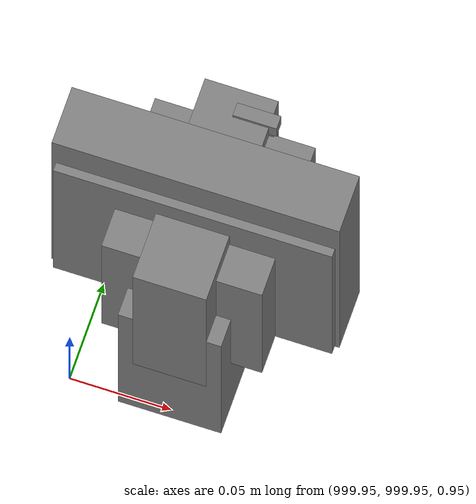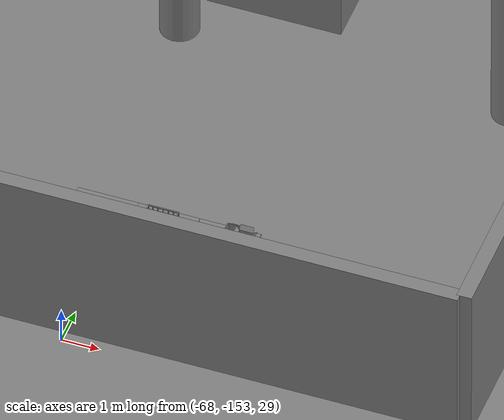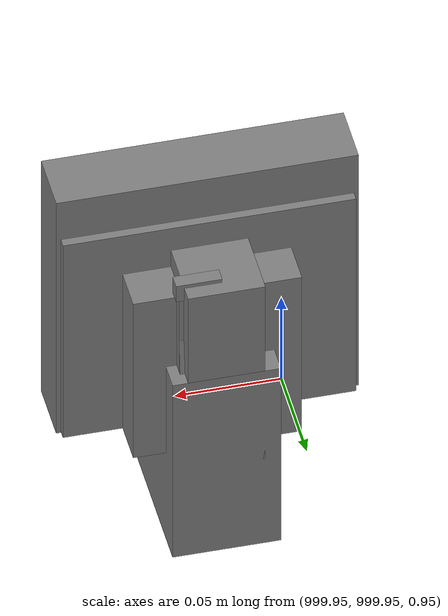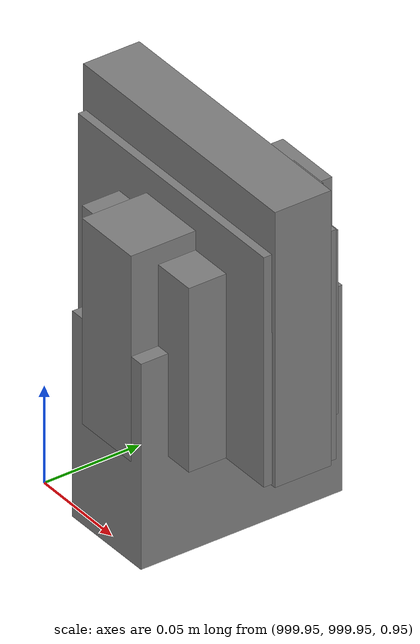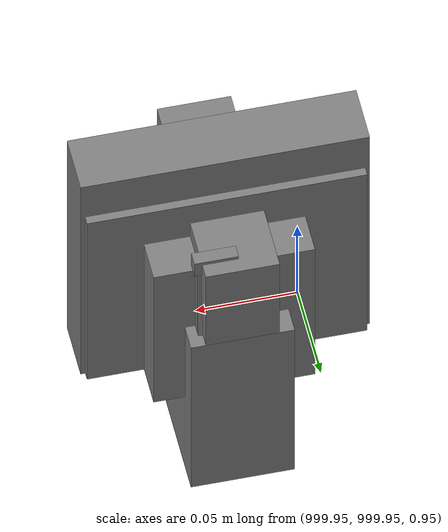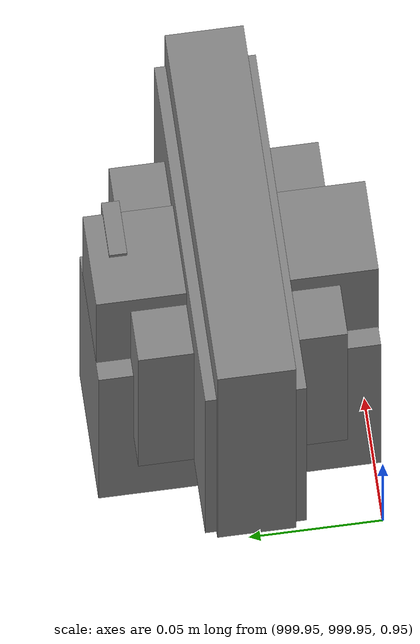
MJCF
<mujoco>
    <option gravity="0.000000000 0.000000000 -9.810000420" timestep="0.0049999999" integrator="implicitfast" density="1.225" viscosity="1.8000001e-05" noslip_iterations="10" iterations="100" sdf_iterations="50">
        <flag multiccd="disable"/>
    </option>
    <size memory="1000M"/>
    <compiler coordinate="local"/>
    <worldbody>
        <light cutoff="30" pos="0 1 1" dir="0 -1 -2"/>
        <light cutoff="30" pos="0 -1 1" dir="0 1 -2"/>
        <body pos="1000.000000000 1000.000000000 1.000000000" euler="0.000000000 0.000000000 180.000000000" name="openloong_gripper_2f85_fix_base_usda_battery_01">
            <geom contype="1" conaffinity="1" density="1000" type="box" material="" rgba="0.500000000 0.500000000 0.500000000 1.000000000" solimp="0.899999976 0.949999988 0.001000000" friction="1.000000000 0.005000000 0.000100000" solref="0.020000000 1.000000000" margin="0" condim="3" group="0" pos="-0.011123657 -0.041940309 0.101691343" quat="1.000000000 0.000000000 0.000000000 0.000000000" size="0.010800000 0.003375000 0.004725000" name="openloong_gripper_2f85_fix_base_usda_geom_A0561B6E_326D_43CC_B824_12711043B32B"/>
            <geom contype="1" conaffinity="1" density="1000" type="box" material="" rgba="0.500000000 0.500000000 0.500000000 1.000000000" solimp="0.899999976 0.949999988 0.001000000" friction="1.000000000 0.005000000 0.000100000" solref="0.020000000 1.000000000" margin="0" condim="3" group="0" pos="-0.010876465 -0.044247437 0.047066893" quat="0.998702705 -0.050920475 0.000000000 0.000000000" size="0.009450001 0.002700000 0.024975000" name="openloong_gripper_2f85_fix_base_usda_geom_07C4404C_0371_4045_A8E3_581ED7237B2C"/>
            <geom contype="1" conaffinity="1" density="1000" type="box" material="" rgba="0.500000000 0.500000000 0.500000000 1.000000000" solimp="0.899999976 0.949999988 0.001000000" friction="1.000000000 0.005000000 0.000100000" solref="0.020000000 1.000000000" margin="0" condim="3" group="0" pos="-0.001235962 -0.000659180 0.047381196" quat="1.000000000 0.000000000 0.000000000 0.000000000" size="0.039420001 0.039150000 0.047250003" name="openloong_gripper_2f85_fix_base_usda_geom_F213AB48_9521_494D_869B_DAEC4A77B778"/>
            <geom contype="1" conaffinity="1" density="1000" type="box" material="" rgba="0.500000000 0.500000000 0.500000000 1.000000000" solimp="0.899999976 0.949999988 0.001000000" friction="1.000000000 0.005000000 0.000100000" solref="0.020000000 1.000000000" margin="0" condim="3" group="0" pos="-0.010876465 -0.039138794 0.009851727" quat="1.000000000 0.000000000 0.000000000 0.000000000" size="0.009450001 0.010800000 0.013500000" name="openloong_gripper_2f85_fix_base_usda_geom_E545A4FD_EC51_4771_B04E_1B3F30BF19C2"/>
            <geom contype="1" conaffinity="1" density="1000" type="box" material="" rgba="0.500000000 0.500000000 0.500000000 1.000000000" solimp="0.899999976 0.949999988 0.001000000" friction="1.000000000 0.005000000 0.000100000" solref="0.020000000 1.000000000" margin="0" condim="3" group="0" pos="-0.010876465 -0.041528322 0.071508206" quat="1.000000000 0.000000000 0.000000000 0.000000000" size="0.009450001 0.002700000 0.027000001" name="openloong_gripper_2f85_fix_base_usda_geom_B7C11049_4057_45AC_91E5_3DE2E4E9C569"/>
            <freejoint name="openloong_gripper_2f85_fix_base_usda_battery_01_joint"/>
            <site size="0.005000000 0.005000000 0.005000000" rgba="0.500000000 0.500000000 0.500000000 1.000000000" pos="0.000000000 0.000000000 0.000000000" quat="0.999961913 0.008726500 0.000000000 0.000000000" group="0" type="sphere" name="openloong_gripper_2f85_fix_base_usda_battery_01site"/>
        </body>
        <body pos="1000.000000000 1000.000000000 1.000000000" euler="0.000000000 0.000000000 180.000000000" name="openloong_gripper_2f85_fix_base_usda_wifi_box">
            <geom contype="1" conaffinity="1" density="1000" type="box" material="" rgba="0.500000000 0.500000000 0.500000000 1.000000000" solimp="0.899999976 0.949999988 0.001000000" friction="1.000000000 0.005000000 0.000100000" solref="0.020000000 1.000000000" margin="0" condim="3" group="0" pos="0.000000000 0.000000000 0.058978677" quat="0.000000000 0.000000047 0.000000000 1.000000000" size="0.068499997 0.018999999 0.059000000" name="openloong_gripper_2f85_fix_base_usda_geom_D4095398_3028_4081_ABAA_F68ED6E70CEB"/>
            <freejoint name="openloong_gripper_2f85_fix_base_usda_wifi_box_joint"/>
            <site size="0.005000000 0.005000000 0.005000000" rgba="0.500000000 0.500000000 0.500000000 1.000000000" pos="0.000000000 0.000000000 0.000000000" quat="0.999961913 0.008726500 0.000000000 0.000000000" group="0" type="sphere" name="openloong_gripper_2f85_fix_base_usda_wifi_boxsite"/>
        </body>
        <body pos="-65.913742065 -149.788986206 31.163784027" euler="161.528640747 -1.483662367 -71.540100098" mocap="true" name="spotlight6_SpotLight"/>
        <body pos="1000.000000000 1000.000000000 1.000000000" euler="0.000011953 0.000005123 -179.999984741" name="openloong_gripper_2f85_fix_base_usda_intel_box">
            <geom contype="1" conaffinity="1" density="1000" type="box" material="" rgba="0.500000000 0.500000000 0.500000000 1.000000000" solimp="0.899999976 0.949999988 0.001000000" friction="1.000000000 0.005000000 0.000100000" solref="0.020000000 1.000000000" margin="0" condim="3" group="0" pos="0.000000000 -0.000067139 0.000082284" quat="0.707106709 0.000000225 0.000000253 0.707106650" size="0.052800003 0.025300000 0.052800003" name="openloong_gripper_2f85_fix_base_usda_geom_8A18F0F0_78CE_4BFA_BF93_39E545883ACD"/>
            <freejoint name="openloong_gripper_2f85_fix_base_usda_intel_box_joint"/>
            <site size="0.005000000 0.005000000 0.005000000" rgba="0.500000000 0.500000000 0.500000000 1.000000000" pos="0.000000000 0.000000000 0.000000000" quat="0.999961913 0.008726500 0.000000000 0.000000000" group="0" type="sphere" name="openloong_gripper_2f85_fix_base_usda_intel_boxsite"/>
        </body>
        <body pos="1000.000000000 1000.000000000 1.000000000" euler="0.000000000 0.000000000 180.000000000" name="openloong_gripper_2f85_fix_base_usda_cpu_fan">
            <geom contype="1" conaffinity="1" density="1000" type="box" material="" rgba="0.500000000 0.500000000 0.500000000 1.000000000" solimp="0.899999976 0.949999988 0.001000000" friction="1.000000000 0.005000000 0.000100000" solref="0.020000000 1.000000000" margin="0" condim="3" group="0" pos="0.000000000 0.000000000 0.070034981" quat="0.000000000 0.000000000 0.000000000 1.000000000" size="0.070700005 0.014699999 0.070700005" name="openloong_gripper_2f85_fix_base_usda_geom_DD0796E9_C8FA_4945_B55C_F4AFCE33A52C"/>
            <freejoint name="openloong_gripper_2f85_fix_base_usda_cpu_fan_joint"/>
            <site size="0.005000000 0.005000000 0.005000000" rgba="0.500000000 0.500000000 0.500000000 1.000000000" pos="0.000000000 0.000000000 0.000000000" quat="0.999961913 0.008726535 0.000000000 0.000000000" group="0" type="sphere" name="openloong_gripper_2f85_fix_base_usda_cpu_fancsite"/>
        </body>
        <body pos="1000.000000000 999.999938965 1.000000000" euler="0.000000000 0.000000000 180.000000000" name="openloong_gripper_2f85_fix_base_usda_intelcore_i5">
            <geom contype="1" conaffinity="1" density="1000" type="box" material="" rgba="0.500000000 0.500000000 0.500000000 1.000000000" solimp="0.899999976 0.949999988 0.001000000" friction="1.000000000 0.005000000 0.000100000" solref="0.020000000 1.000000000" margin="0" condim="3" group="0" pos="0.000000000 0.000000000 0.051722717" quat="0.707106709 0.000000000 0.000000000 -0.707106769" size="0.052800000 0.018080002 0.052800000" name="openloong_gripper_2f85_fix_base_usda_geom_F8AE6EFE_E66A_4DDA_A602_DD68126F9CD6"/>
            <freejoint name="openloong_gripper_2f85_fix_base_usda_intelcore_i5_joint"/>
            <site size="0.005000000 0.005000000 0.005000000" rgba="0.500000000 0.500000000 0.500000000 1.000000000" pos="0.000000000 0.000000000 0.000000000" quat="0.999961913 0.008726534 0.000000000 0.000000000" group="0" type="sphere" name="openloong_gripper_2f85_fix_base_usda_intelcore_i5site"/>
        </body>
        <body pos="-66.004501343 -149.279113770 31.171840668" euler="-47.933460236 -84.590148926 4.582194805" mocap="true" name="spotlight1_SpotLight"/>
        <body pos="-66.246711731 -149.196014404 31.164585114" euler="10.564297676 27.023366928 -121.282417297" mocap="true" name="spotlight2_SpotLight"/>
        <body pos="-64.866622925 -149.383972168 30.183746338" euler="89.999984741 89.999946594 0.000000000" name="openloong_gripper_2f85_fix_base_usda_bluebox_01">
            <geom contype="1" conaffinity="1" density="1000" type="box" material="" rgba="0.500000000 0.500000000 0.500000000 1.000000000" solimp="0.899999976 0.949999988 0.001000000" friction="1.000000000 0.005000000 0.000100000" solref="0.020000000 1.000000000" margin="0" condim="3" group="0" pos="0.276580811 0.187225342 0.000068665" quat="0.707106948 0.000077471 0.707106352 0.000077486" size="0.100000001 0.057999998 0.010000000" name="openloong_gripper_2f85_fix_base_usda_geom_36806CEF_1074_47EE_8135_FA06751E86C1"/>
            <geom contype="1" conaffinity="1" density="1000" type="box" material="" rgba="0.500000000 0.500000000 0.500000000 1.000000000" solimp="0.899999976 0.949999988 0.001000000" friction="1.000000000 0.005000000 0.000100000" solref="0.020000000 1.000000000" margin="0" condim="3" group="0" pos="0.000000000 0.002883911 0.000000000" quat="0.999999881 0.000000000 0.000000000 0.000000000" size="0.254000008 0.003000000 0.172000006" name="openloong_gripper_2f85_fix_base_usda_geom_7A67F747_A301_4A73_8866_FA02C4D8FFB8"/>
            <geom contype="1" conaffinity="1" density="1000" type="box" material="" rgba="0.500000000 0.500000000 0.500000000 1.000000000" solimp="0.899999976 0.949999988 0.001000000" friction="1.000000000 0.005000000 0.000100000" solref="0.020000000 1.000000000" margin="0" condim="3" group="0" pos="0.000000000 0.124874115 0.173484802" quat="0.999796331 0.020176515 -0.000000015 0.000000030" size="0.259999990 0.119999997 0.007000000" name="openloong_gripper_2f85_fix_base_usda_geom_E7A33700_3C6C_4CA2_A8E7_BDD56CC9B99C"/>
            <geom contype="1" conaffinity="1" density="1000" type="box" material="" rgba="0.500000000 0.500000000 0.500000000 1.000000000" solimp="0.899999976 0.949999988 0.001000000" friction="1.000000000 0.005000000 0.000100000" solref="0.020000000 1.000000000" margin="0" condim="3" group="0" pos="0.000000000 0.124874115 -0.173469543" quat="0.999796331 -0.020176545 -0.000000015 0.000000000" size="0.259999990 0.119999997 0.007000000" name="openloong_gripper_2f85_fix_base_usda_geom_F5866727_82B1_46B5_BCC6_9D69A333C6EE"/>
            <geom contype="1" conaffinity="1" density="1000" type="box" material="" rgba="0.500000000 0.500000000 0.500000000 1.000000000" solimp="0.899999976 0.949999988 0.001000000" friction="1.000000000 0.005000000 0.000100000" solref="0.020000000 1.000000000" margin="0" condim="3" group="0" pos="0.000000000 0.214008331 0.188980103" quat="0.999912977 0.013176724 0.000000015 0.000000000" size="0.259999990 0.029999999 0.012500000" name="openloong_gripper_2f85_fix_base_usda_geom_6560A2E0_7253_473F_AE9B_B9F5DDCCF45B"/>
            <geom contype="1" conaffinity="1" density="1000" type="box" material="" rgba="0.500000000 0.500000000 0.500000000 1.000000000" solimp="0.899999976 0.949999988 0.001000000" friction="1.000000000 0.005000000 0.000100000" solref="0.020000000 1.000000000" margin="0" condim="3" group="0" pos="-0.258361816 0.125289917 0.001876831" quat="0.702796936 -0.020792112 0.710783124 0.020769298" size="0.189999998 0.119999997 0.009000000" name="openloong_gripper_2f85_fix_base_usda_geom_24ACF2C7_A101_4CCB_AEDE_F44D0043FCC4"/>
            <geom contype="1" conaffinity="1" density="1000" type="box" material="" rgba="0.500000000 0.500000000 0.500000000 1.000000000" solimp="0.899999976 0.949999988 0.001000000" friction="1.000000000 0.005000000 0.000100000" solref="0.020000000 1.000000000" margin="0" condim="3" group="0" pos="0.000000000 0.214008331 -0.188980103" quat="0.999912977 -0.013176769 0.000000030 0.000000015" size="0.259999990 0.029999999 0.012500000" name="openloong_gripper_2f85_fix_base_usda_geom_CE103AB1_7E11_4D38_97BB_7DC66DB1FDDB"/>
            <geom contype="1" conaffinity="1" density="1000" type="box" material="" rgba="0.500000000 0.500000000 0.500000000 1.000000000" solimp="0.899999976 0.949999988 0.001000000" friction="1.000000000 0.005000000 0.000100000" solref="0.020000000 1.000000000" margin="0" condim="3" group="0" pos="-0.276611328 0.187225342 0.000068665" quat="0.707106650 0.000077441 0.707106709 0.000077456" size="0.100000001 0.057999998 0.010000000" name="openloong_gripper_2f85_fix_base_usda_geom_7974AB90_ED40_4BC5_8757_C284C1606587"/>
            <geom contype="1" conaffinity="1" density="1000" type="box" material="" rgba="0.500000000 0.500000000 0.500000000 1.000000000" solimp="0.899999976 0.949999988 0.001000000" friction="1.000000000 0.005000000 0.000100000" solref="0.020000000 1.000000000" margin="0" condim="3" group="0" pos="0.258331299 0.125289917 0.001876831" quat="0.702851415 0.018856421 0.710823774 -0.019329369" size="0.189999998 0.119999997 0.009000000" name="openloong_gripper_2f85_fix_base_usda_geom_D6F0671B_E046_4D82_8F33_02917C355598"/>
            <freejoint name="openloong_gripper_2f85_fix_base_usda_bluebox_01_joint"/>
            <site size="0.005000000 0.005000000 0.005000000" rgba="0.500000000 0.500000000 0.500000000 1.000000000" pos="0.000000000 0.000000000 0.000000000" quat="0.999961913 0.008726534 0.000000000 0.000000000" group="0" type="sphere" name="openloong_gripper_2f85_fix_base_usda_bluebox_01site"/>
        </body>
        <body pos="-64.496299744 -149.491867065 30.235729218" euler="0.000000000 0.000000000 89.999946594" name="openloong_gripper_2f85_fix_base_usda_cardboardbox_01">
            <geom contype="1" conaffinity="1" density="1000" type="box" material="" rgba="0.500000000 0.500000000 0.500000000 1.000000000" solimp="0.899999976 0.949999988 0.001000000" friction="1.000000000 0.005000000 0.000100000" solref="0.020000000 1.000000000" margin="0" condim="3" group="0" pos="-0.003166199 -0.004086494 0.005052090" quat="1.000000000 0.000000000 0.000000000 0.000000000" size="0.142499998 0.177500010 0.005000000" name="openloong_gripper_2f85_fix_base_usda_geom_B2917B66_5C51_466D_A245_5D97ADA63C9C"/>
            <geom contype="1" conaffinity="1" density="1000" type="box" material="" rgba="0.500000000 0.500000000 0.500000000 1.000000000" solimp="0.899999976 0.949999988 0.001000000" friction="1.000000000 0.005000000 0.000100000" solref="0.020000000 1.000000000" margin="0" condim="3" group="0" pos="-0.003166199 0.170316696 0.150570869" quat="1.000000000 0.000000000 0.000000000 0.000000000" size="0.142499998 0.005000000 0.149999991" name="openloong_gripper_2f85_fix_base_usda_geom_5AFF8412_BD68_4550_A82E_91EE310E5DAE"/>
            <geom contype="1" conaffinity="1" density="1000" type="box" material="" rgba="0.500000000 0.500000000 0.500000000 1.000000000" solimp="0.899999976 0.949999988 0.001000000" friction="1.000000000 0.005000000 0.000100000" solref="0.020000000 1.000000000" margin="0" condim="3" group="0" pos="-0.147399902 -0.005307198 0.150570869" quat="1.000000000 0.000000000 0.000000000 0.000000000" size="0.005000000 0.177500010 0.149999991" name="openloong_gripper_2f85_fix_base_usda_geom_FD0C3148_84E6_427F_8D63_35C529FD4154"/>
            <geom contype="1" conaffinity="1" density="1000" type="box" material="" rgba="0.500000000 0.500000000 0.500000000 1.000000000" solimp="0.899999976 0.949999988 0.001000000" friction="1.000000000 0.005000000 0.000100000" solref="0.020000000 1.000000000" margin="0" condim="3" group="0" pos="0.140275955 -0.005307198 0.150570869" quat="1.000000000 0.000000000 0.000000000 0.000000000" size="0.005000000 0.177500010 0.149999991" name="openloong_gripper_2f85_fix_base_usda_geom_E338AEFE_0AF8_47F0_846F_73C5BAB4EE1B"/>
            <geom contype="1" conaffinity="1" density="1000" type="box" material="" rgba="0.500000000 0.500000000 0.500000000 1.000000000" solimp="0.899999976 0.949999988 0.001000000" friction="1.000000000 0.005000000 0.000100000" solref="0.020000000 1.000000000" margin="0" condim="3" group="0" pos="-0.003166199 -0.181550980 0.150570869" quat="1.000000000 0.000000000 0.000000000 0.000000000" size="0.142499998 0.005000000 0.149999991" name="openloong_gripper_2f85_fix_base_usda_geom_171D083A_3B2E_4661_84A0_0601B9ACE42F"/>
            <freejoint name="openloong_gripper_2f85_fix_base_usda_cardboardbox_01_joint"/>
            <site size="0.005000000 0.005000000 0.005000000" rgba="0.500000000 0.500000000 0.500000000 1.000000000" pos="0.000000000 0.000000000 0.000000000" quat="0.999961913 0.008726535 0.000000000 0.000000000" group="0" type="sphere" name="openloong_gripper_2f85_fix_base_usda_site_30D2C6DA_BE88_44DD_8F1F_7E0B0CAECDCD"/>
            <body pos="0.139160156 -0.004048347 0.301930904" euler="-179.999954224 49.383502960 179.999954224" name="openloong_gripper_2f85_fix_base_usda_A1_006">
                <geom contype="1" conaffinity="1" density="1000" type="box" material="" rgba="0.500000000 0.500000000 0.500000000 1.000000000" solimp="0.899999976 0.949999988 0.001000000" friction="1.000000000 0.005000000 0.000100000" solref="0.020000000 1.000000000" margin="0" condim="3" group="0" pos="-0.071587563 0.000009537 0.001745224" quat="0.999999881 0.000000000 0.000000000 0.000000000" size="0.071249999 0.179999992 0.002500000" name="openloong_gripper_2f85_fix_base_usda_geom_9BD736A0_A52C_484F_BE66_541FBBF2032B"/>
                <joint armature="0" stiffness="0.07" damping="0.0099999998" axis="0.000000 1.000000 0.000000" type="hinge" name="openloong_gripper_2f85_fix_base_usda_A1_006"/>
            </body>
            <body pos="-0.145902634 -0.004086494 0.301938057" euler="-180.000000000 -60.000011444 -180.000000000" name="openloong_gripper_2f85_fix_base_usda_A2_006">
                <geom contype="1" conaffinity="1" density="1000" type="box" material="" rgba="0.500000000 0.500000000 0.500000000 1.000000000" solimp="0.899999976 0.949999988 0.001000000" friction="1.000000000 0.005000000 0.000100000" solref="0.020000000 1.000000000" margin="0" condim="3" group="0" pos="0.071268082 0.000009537 0.002717972" quat="0.000002921 0.000000000 -0.000000030 0.999999881" size="0.071249999 0.179999992 0.002500000" name="openloong_gripper_2f85_fix_base_usda_geom_B61C3DBF_634D_4C46_9C24_7E35A724ACE3"/>
                <joint armature="0" stiffness="0.07" damping="0.0099999998" axis="0.000000 1.000000 0.000000" type="hinge" name="openloong_gripper_2f85_fix_base_usda_A2_006"/>
            </body>
            <body pos="-0.003385544 0.175991058 0.301930904" euler="-125.858116150 -0.000004561 0.000002331" name="openloong_gripper_2f85_fix_base_usda_B2_006">
                <geom contype="1" conaffinity="1" density="1000" type="box" material="" rgba="0.500000000 0.500000000 0.500000000 1.000000000" solimp="0.899999976 0.949999988 0.001000000" friction="1.000000000 0.005000000 0.000100000" solref="0.020000000 1.000000000" margin="0" condim="3" group="0" pos="0.000009537 -0.070939064 -0.002470016" quat="0.999614120 0.027776197 -0.000000015 0.000000030" size="0.137500003 0.064999998 0.005000000" name="openloong_gripper_2f85_fix_base_usda_geom_3EE0CA02_75D2_4364_964B_7B8C4F2F7D26"/>
                <joint armature="0" stiffness="0.07" damping="0.0099999998" axis="1.000000 0.000000 0.000000" type="hinge" name="openloong_gripper_2f85_fix_base_usda_B2_006"/>
            </body>
            <body pos="-0.003385544 -0.184140205 0.301938057" euler="147.805557251 0.000000000 0.000000000" name="openloong_gripper_2f85_fix_base_usda_B1_006">
                <geom contype="1" conaffinity="1" density="1000" type="box" material="" rgba="0.500000000 0.500000000 0.500000000 1.000000000" solimp="0.899999976 0.949999988 0.001000000" friction="1.000000000 0.005000000 0.000100000" solref="0.020000000 1.000000000" margin="0" condim="3" group="0" pos="-0.000028610 0.070202351 -0.002703667" quat="0.999614179 -0.027776167 0.000000000 0.000000000" size="0.137500003 0.064999998 0.005000000" name="openloong_gripper_2f85_fix_base_usda_geom_87834E1E_DC58_4E94_BBF3_92826C3C5F52"/>
                <joint armature="0" stiffness="0.07" damping="0.0099999998" axis="1.000000 0.000000 0.000000" type="hinge" name="openloong_gripper_2f85_fix_base_usda_B1_006"/>
            </body>
        </body>
        <body pos="-65.882858276 -149.481979370 30.229999542" euler="-64.487716675 0.000000000 0.000000000" name="openloong_gripper_2f85_fix_base_usda_Barcode">
            <geom contype="1" conaffinity="1" density="1000" type="box" material="" rgba="0.500000000 0.500000000 0.500000000 1.000000000" solimp="0.899999976 0.949999988 0.001000000" friction="1.000000000 0.005000000 0.000100000" solref="0.020000000 1.000000000" margin="0" condim="3" group="0" pos="0.000000000 0.013038635 0.001419067" quat="0.000000000 0.000000000 0.000000000 1.000000119" size="0.034000002 0.010000000 0.017999999" name="openloong_gripper_2f85_fix_base_usda_geom_060E84E9_8ED7_4FD5_B0C0_67302ABBC5DE"/>
            <geom contype="1" conaffinity="1" density="1000" type="box" material="" rgba="0.500000000 0.500000000 0.500000000 1.000000000" solimp="0.899999976 0.949999988 0.001000000" friction="1.000000000 0.005000000 0.000100000" solref="0.020000000 1.000000000" margin="0" condim="3" group="0" pos="0.000000000 -0.035301208 -0.007095337" quat="0.000000000 0.000000000 -0.043619365 0.999048233" size="0.028999999 0.010000000 0.020000000" name="openloong_gripper_2f85_fix_base_usda_geom_AE774B5A_A231_4CE2_AE25_E918D69C6D56"/>
            <geom contype="1" conaffinity="1" density="1000" type="box" material="" rgba="0.500000000 0.500000000 0.500000000 1.000000000" solimp="0.899999976 0.949999988 0.001000000" friction="1.000000000 0.005000000 0.000100000" solref="0.020000000 1.000000000" margin="0" condim="3" group="0" pos="0.000000000 -0.043411255 -0.011749268" quat="0.922262907 0.386563420 0.000000000 0.000000000" size="0.026000001 0.010000000 0.020000000" name="openloong_gripper_2f85_fix_base_usda_geom_568509F9_501F_47CB_9328_BF2ABF0AB69C"/>
            <geom contype="1" conaffinity="1" density="1000" type="box" material="" rgba="0.500000000 0.500000000 0.500000000 1.000000000" solimp="0.899999976 0.949999988 0.001000000" friction="1.000000000 0.005000000 0.000100000" solref="0.020000000 1.000000000" margin="0" condim="3" group="0" pos="0.000000000 -0.016967773 -0.031860352" quat="0.000000000 0.000000000 0.000000000 1.000000119" size="0.008000000 0.010000000 0.013000000" name="openloong_gripper_2f85_fix_base_usda_geom_80DF6974_863C_4507_AEC6_92F5AD3201C6"/>
            <geom contype="1" conaffinity="1" density="1000" type="box" material="" rgba="0.500000000 0.500000000 0.500000000 1.000000000" solimp="0.899999976 0.949999988 0.001000000" friction="1.000000000 0.005000000 0.000100000" solref="0.020000000 1.000000000" margin="0" condim="3" group="0" pos="0.000000000 -0.001869202 0.000312805" quat="0.953716993 0.300705761 0.000000000 0.000000000" size="0.032000002 0.010000000 0.018999999" name="openloong_gripper_2f85_fix_base_usda_geom_45124585_4505_4CCD_B61A_C6A2007AD3C1"/>
            <geom contype="1" conaffinity="1" density="1000" type="box" material="" rgba="0.500000000 0.500000000 0.500000000 1.000000000" solimp="0.899999976 0.949999988 0.001000000" friction="1.000000000 0.005000000 0.000100000" solref="0.020000000 1.000000000" margin="0" condim="3" group="0" pos="0.000000000 -0.019531250 -0.003173828" quat="0.953716993 0.300705761 0.000000000 0.000000000" size="0.030999999 0.010000000 0.020000000" name="openloong_gripper_2f85_fix_base_usda_geom_60E86A3B_3AF7_459A_B564_9F8555DC6FA3"/>
            <geom contype="1" conaffinity="1" density="1000" type="box" material="" rgba="0.500000000 0.500000000 0.500000000 1.000000000" solimp="0.899999976 0.949999988 0.001000000" friction="1.000000000 0.005000000 0.000100000" solref="0.020000000 1.000000000" margin="0" condim="3" group="0" pos="0.000000000 -0.035301208 -0.007095337" quat="0.953716993 0.300705761 0.000000000 0.000000000" size="0.028999999 0.010000000 0.020000000" name="openloong_gripper_2f85_fix_base_usda_geom_9CAE3212_5705_403B_892A_12E0F3AA8AB2"/>
            <geom contype="1" conaffinity="1" density="1000" type="box" material="" rgba="0.500000000 0.500000000 0.500000000 1.000000000" solimp="0.899999976 0.949999988 0.001000000" friction="1.000000000 0.005000000 0.000100000" solref="0.020000000 1.000000000" margin="0" condim="3" group="0" pos="0.000000000 -0.042617798 -0.071121216" quat="0.000000000 0.000000000 0.000000000 1.000000119" size="0.013000000 0.021000000 0.059999999" name="openloong_gripper_2f85_fix_base_usda_geom_8D78F6AF_C0A6_4F65_8493_BF5C5546B935"/>
            <freejoint name="openloong_gripper_2f85_fix_base_usda_Barcode_joint"/>
            <site size="0.005000000 0.005000000 0.005000000" rgba="0.500000000 0.500000000 0.500000000 1.000000000" pos="0.000000000 0.000000000 0.000000000" quat="1.000000000 0.000000000 0.000000000 0.000000000" group="0" type="sphere" name="openloong_gripper_2f85_fix_base_usda_Barcode_site"/>
        </body>
        <body pos="-66.745018005 -149.392349243 30.184000015" euler="0.000000000 0.000000000 89.999946594" name="[22330975247882]_Basket_01">
            <geom contype="1" conaffinity="1" density="1000" type="box" material="" rgba="0.500000000 0.500000000 0.500000000 1.000000000" solimp="0.899999976 0.949999988 0.001000000" friction="1.000000000 0.005000000 0.000100000" solref="0.020000000 1.000000000" margin="0" condim="3" group="0" pos="-0.052425385 0.389207840 0.089787483" quat="0.707107008 0.000000000 0.000000000 0.707106411" size="0.014249999 0.014249999 0.059999999" name="[22330975247882]_geom_C795124E_F15A_45C8_8932_94961992A3B5"/>
            <geom contype="1" conaffinity="1" density="1000" type="box" material="" rgba="0.500000000 0.500000000 0.500000000 1.000000000" solimp="0.899999976 0.949999988 0.001000000" friction="1.000000000 0.005000000 0.000100000" solref="0.020000000 1.000000000" margin="0" condim="3" group="0" pos="0.264015198 -0.133043289 0.089787483" quat="0.707107008 0.000000000 0.000000000 0.707106411" size="0.014249999 0.014249999 0.059999999" name="[22330975247882]_geom_8EB85319_425B_4766_ABFA_08F34D4DE3F6"/>
            <geom contype="1" conaffinity="1" density="1000" type="box" material="" rgba="0.500000000 0.500000000 0.500000000 1.000000000" solimp="0.899999976 0.949999988 0.001000000" friction="1.000000000 0.005000000 0.000100000" solref="0.020000000 1.000000000" margin="0" condim="3" group="0" pos="-0.264015198 -0.265548706 0.089793205" quat="0.707107008 0.000000000 0.000000000 0.707106411" size="0.014249999 0.014249999 0.059999999" name="[22330975247882]_geom_7612FB1D_5210_46AB_9F9E_852E9A87453B"/>
            <geom contype="1" conaffinity="1" density="1000" type="box" material="" rgba="0.500000000 0.500000000 0.500000000 1.000000000" solimp="0.899999976 0.949999988 0.001000000" friction="1.000000000 0.005000000 0.000100000" solref="0.020000000 1.000000000" margin="0" condim="3" group="0" pos="-0.160263062 -0.389322281 0.089793205" quat="0.707107008 0.000000000 0.000000000 0.707106411" size="0.014249999 0.014249999 0.059999999" name="[22330975247882]_geom_51F45C8D_E081_4E28_856D_D3A5398BA239"/>
            <geom contype="1" conaffinity="1" density="1000" type="box" material="" rgba="0.500000000 0.500000000 0.500000000 1.000000000" solimp="0.899999976 0.949999988 0.001000000" friction="1.000000000 0.005000000 0.000100000" solref="0.020000000 1.000000000" margin="0" condim="3" group="0" pos="0.162265778 -0.389322281 0.089787483" quat="0.707107008 0.000000000 0.000000000 0.707106411" size="0.014249999 0.014249999 0.059999999" name="[22330975247882]_geom_39105374_1285_4C80_9379_B3C3DA0E5AA0"/>
            <geom contype="1" conaffinity="1" density="1000" type="box" material="" rgba="0.500000000 0.500000000 0.500000000 1.000000000" solimp="0.899999976 0.949999988 0.001000000" friction="1.000000000 0.005000000 0.000100000" solref="0.020000000 1.000000000" margin="0" condim="3" group="0" pos="0.264015198 0.389207840 0.089787483" quat="0.707107008 0.000000000 0.000000000 0.707106411" size="0.014249999 0.014249999 0.059999999" name="[22330975247882]_geom_4B0A89B7_6F49_4A63_A6AE_7018A1779F23"/>
            <geom contype="1" conaffinity="1" density="1000" type="box" material="" rgba="0.500000000 0.500000000 0.500000000 1.000000000" solimp="0.899999976 0.949999988 0.001000000" friction="1.000000000 0.005000000 0.000100000" solref="0.020000000 1.000000000" margin="0" condim="3" group="0" pos="-0.264015198 -0.133043289 0.089793205" quat="0.707107008 0.000000000 0.000000000 0.707106411" size="0.014249999 0.014249999 0.059999999" name="[22330975247882]_geom_A0762217_89A5_40EE_BA40_4A3E29CE3A90"/>
            <geom contype="1" conaffinity="1" density="1000" type="box" material="" rgba="0.500000000 0.500000000 0.500000000 1.000000000" solimp="0.899999976 0.949999988 0.001000000" friction="1.000000000 0.005000000 0.000100000" solref="0.020000000 1.000000000" margin="0" condim="3" group="0" pos="-0.264026642 0.269256592 0.089793205" quat="0.707107008 0.000000000 0.000000000 0.707106411" size="0.014249999 0.014249999 0.059999999" name="[22330975247882]_geom_622DB465_13DD_4AE7_9E3F_6361CCE73B4D"/>
            <geom contype="1" conaffinity="1" density="1000" type="box" material="" rgba="0.500000000 0.500000000 0.500000000 1.000000000" solimp="0.899999976 0.949999988 0.001000000" friction="1.000000000 0.005000000 0.000100000" solref="0.020000000 1.000000000" margin="0" condim="3" group="0" pos="0.054462433 0.389207840 0.089787483" quat="0.707107008 0.000000000 0.000000000 0.707106411" size="0.014249999 0.014249999 0.059999999" name="[22330975247882]_geom_9E1A2516_50EC_461C_8D9B_D7A55AA054A5"/>
            <geom contype="1" conaffinity="1" density="1000" type="box" material="" rgba="0.500000000 0.500000000 0.500000000 1.000000000" solimp="0.899999976 0.949999988 0.001000000" friction="1.000000000 0.005000000 0.000100000" solref="0.020000000 1.000000000" margin="0" condim="3" group="0" pos="0.054462433 -0.389322281 0.089787483" quat="0.707107008 0.000000000 0.000000000 0.707106411" size="0.014249999 0.014249999 0.059999999" name="[22330975247882]_geom_7C3CC2E9_52D2_4B1B_88FB_7C5B8AEC24DF"/>
            <geom contype="1" conaffinity="1" density="1000" type="box" material="" rgba="0.500000000 0.500000000 0.500000000 1.000000000" solimp="0.899999976 0.949999988 0.001000000" friction="1.000000000 0.005000000 0.000100000" solref="0.020000000 1.000000000" margin="0" condim="3" group="0" pos="0.264015198 0.269256592 0.089793205" quat="0.707107008 0.000000000 0.000000000 0.707106411" size="0.014249999 0.014249999 0.059999999" name="[22330975247882]_geom_57FED67A_D7ED_48CE_BFAD_3084CB4A5215"/>
            <geom contype="1" conaffinity="1" density="1000" type="box" material="" rgba="0.500000000 0.500000000 0.500000000 1.000000000" solimp="0.899999976 0.949999988 0.001000000" friction="1.000000000 0.005000000 0.000100000" solref="0.020000000 1.000000000" margin="0" condim="3" group="0" pos="0.264015198 -0.389322281 0.089787483" quat="0.707107008 0.000000000 0.000000000 0.707106411" size="0.014249999 0.014249999 0.059999999" name="[22330975247882]_geom_9AC52A85_E01F_44AC_9C88_F3C503A92D4C"/>
            <geom contype="1" conaffinity="1" density="1000" type="box" material="" rgba="0.500000000 0.500000000 0.500000000 1.000000000" solimp="0.899999976 0.949999988 0.001000000" friction="1.000000000 0.005000000 0.000100000" solref="0.020000000 1.000000000" margin="0" condim="3" group="0" pos="0.000000000 0.000000000 0.015998840" quat="0.707107008 0.000000000 0.000000000 0.707106411" size="0.403499991 0.279000014 0.015750000" name="[22330975247882]_geom_96633F3C_3656_4F84_A25E_5A32619BA103"/>
            <geom contype="1" conaffinity="1" density="1000" type="box" material="" rgba="0.500000000 0.500000000 0.500000000 1.000000000" solimp="0.899999976 0.949999988 0.001000000" friction="1.000000000 0.005000000 0.000100000" solref="0.020000000 1.000000000" margin="0" condim="3" group="0" pos="0.000000000 -0.389476776 0.163619041" quat="0.707107008 0.000000000 0.000000000 0.707106411" size="0.015000000 0.277500004 0.015750000" name="[22330975247882]_geom_E4C51B5F_EF65_40CF_A4DF_D09AE14B71CF"/>
            <geom contype="1" conaffinity="1" density="1000" type="box" material="" rgba="0.500000000 0.500000000 0.500000000 1.000000000" solimp="0.899999976 0.949999988 0.001000000" friction="1.000000000 0.005000000 0.000100000" solref="0.020000000 1.000000000" margin="0" condim="3" group="0" pos="0.162265778 0.389207840 0.089787483" quat="0.707107008 0.000000000 0.000000000 0.707106411" size="0.014249999 0.014249999 0.059999999" name="[22330975247882]_geom_5D4568FD_5E34_4069_ADD9_F879D7B4908E"/>
            <geom contype="1" conaffinity="1" density="1000" type="box" material="" rgba="0.500000000 0.500000000 0.500000000 1.000000000" solimp="0.899999976 0.949999988 0.001000000" friction="1.000000000 0.005000000 0.000100000" solref="0.020000000 1.000000000" margin="0" condim="3" group="0" pos="0.000000000 0.389471054 0.163619041" quat="0.707107008 0.000000000 0.000000000 0.707106411" size="0.015000000 0.277500004 0.015750000" name="[22330975247882]_geom_DD5697E9_94CD_4905_9C71_76D09A3C1367"/>
            <geom contype="1" conaffinity="1" density="1000" type="box" material="" rgba="0.500000000 0.500000000 0.500000000 1.000000000" solimp="0.899999976 0.949999988 0.001000000" friction="1.000000000 0.005000000 0.000100000" solref="0.020000000 1.000000000" margin="0" condim="3" group="0" pos="-0.263511658 0.000000000 0.163619041" quat="0.707107008 0.000000000 0.000000000 0.707106411" size="0.403499991 0.015000000 0.015750000" name="[22330975247882]_geom_8E7B8776_1DEF_4A07_9F56_40A149FED3E1"/>
            <geom contype="1" conaffinity="1" density="1000" type="box" material="" rgba="0.500000000 0.500000000 0.500000000 1.000000000" solimp="0.899999976 0.949999988 0.001000000" friction="1.000000000 0.005000000 0.000100000" solref="0.020000000 1.000000000" margin="0" condim="3" group="0" pos="-0.264015198 0.141334534 0.089793205" quat="0.707107008 0.000000000 0.000000000 0.707106411" size="0.014249999 0.014249999 0.059999999" name="[22330975247882]_geom_A25533F8_0036_4D87_876B_F9239C8B04A8"/>
            <geom contype="1" conaffinity="1" density="1000" type="box" material="" rgba="0.500000000 0.500000000 0.500000000 1.000000000" solimp="0.899999976 0.949999988 0.001000000" friction="1.000000000 0.005000000 0.000100000" solref="0.020000000 1.000000000" margin="0" condim="3" group="0" pos="0.264015198 -0.265548706 0.089787483" quat="0.707107008 0.000000000 0.000000000 0.707106411" size="0.014249999 0.014249999 0.059999999" name="[22330975247882]_geom_DAD684BD_166B_4EAE_BC89_36628B78F0F8"/>
            <geom contype="1" conaffinity="1" density="1000" type="box" material="" rgba="0.500000000 0.500000000 0.500000000 1.000000000" solimp="0.899999976 0.949999988 0.001000000" friction="1.000000000 0.005000000 0.000100000" solref="0.020000000 1.000000000" margin="0" condim="3" group="0" pos="-0.160263062 0.389207840 0.089787483" quat="0.707107008 0.000000000 0.000000000 0.707106411" size="0.014249999 0.014249999 0.059999999" name="[22330975247882]_geom_C940D5C6_F9E4_4A80_8B25_65CB63DEE513"/>
            <geom contype="1" conaffinity="1" density="1000" type="box" material="" rgba="0.500000000 0.500000000 0.500000000 1.000000000" solimp="0.899999976 0.949999988 0.001000000" friction="1.000000000 0.005000000 0.000100000" solref="0.020000000 1.000000000" margin="0" condim="3" group="0" pos="-0.052425385 -0.389322281 0.089787483" quat="0.707107008 0.000000000 0.000000000 0.707106411" size="0.014249999 0.014249999 0.059999999" name="[22330975247882]_geom_9B028507_EA59_47D0_BB92_11FDB2C25306"/>
            <geom contype="1" conaffinity="1" density="1000" type="box" material="" rgba="0.500000000 0.500000000 0.500000000 1.000000000" solimp="0.899999976 0.949999988 0.001000000" friction="1.000000000 0.005000000 0.000100000" solref="0.020000000 1.000000000" margin="0" condim="3" group="0" pos="-0.264026642 -0.389322281 0.089793205" quat="0.707107008 0.000000000 0.000000000 0.707106411" size="0.014249999 0.014249999 0.059999999" name="[22330975247882]_geom_D7A042AB_B52A_4594_BC93_E72A255140B1"/>
            <geom contype="1" conaffinity="1" density="1000" type="box" material="" rgba="0.500000000 0.500000000 0.500000000 1.000000000" solimp="0.899999976 0.949999988 0.001000000" friction="1.000000000 0.005000000 0.000100000" solref="0.020000000 1.000000000" margin="0" condim="3" group="0" pos="0.264015198 0.141334534 0.089787483" quat="0.707107008 0.000000000 0.000000000 0.707106411" size="0.014249999 0.014249999 0.059999999" name="[22330975247882]_geom_EF56789A_C020_4F52_8AB1_9026A4037677"/>
            <geom contype="1" conaffinity="1" density="1000" type="box" material="" rgba="0.500000000 0.500000000 0.500000000 1.000000000" solimp="0.899999976 0.949999988 0.001000000" friction="1.000000000 0.005000000 0.000100000" solref="0.020000000 1.000000000" margin="0" condim="3" group="0" pos="-0.264015198 0.389207840 0.089793205" quat="0.707107008 0.000000000 0.000000000 0.707106411" size="0.014249999 0.014249999 0.059999999" name="[22330975247882]_geom_05980499_CBCD_48F7_8818_78BEF40402B2"/>
            <geom contype="1" conaffinity="1" density="1000" type="box" material="" rgba="0.500000000 0.500000000 0.500000000 1.000000000" solimp="0.899999976 0.949999988 0.001000000" friction="1.000000000 0.005000000 0.000100000" solref="0.020000000 1.000000000" margin="0" condim="3" group="0" pos="0.264015198 0.004480362 0.089787483" quat="0.707107008 0.000000000 0.000000000 0.707106411" size="0.014249999 0.014249999 0.059999999" name="[22330975247882]_geom_5558ECDF_7F83_4544_899F_3B591C710E93"/>
            <geom contype="1" conaffinity="1" density="1000" type="box" material="" rgba="0.500000000 0.500000000 0.500000000 1.000000000" solimp="0.899999976 0.949999988 0.001000000" friction="1.000000000 0.005000000 0.000100000" solref="0.020000000 1.000000000" margin="0" condim="3" group="0" pos="0.263694763 -0.000011444 0.163619041" quat="0.707107008 0.000000000 0.000000000 0.707106411" size="0.403499991 0.015000000 0.015750000" name="[22330975247882]_geom_00D62A0D_F63E_4F0B_A8BF_536E0C883FF8"/>
            <geom contype="1" conaffinity="1" density="1000" type="box" material="" rgba="0.500000000 0.500000000 0.500000000 1.000000000" solimp="0.899999976 0.949999988 0.001000000" friction="1.000000000 0.005000000 0.000100000" solref="0.020000000 1.000000000" margin="0" condim="3" group="0" pos="-0.264015198 0.004480362 0.089793205" quat="0.707107008 0.000000000 0.000000000 0.707106411" size="0.014249999 0.014249999 0.059999999" name="[22330975247882]_geom_16D5550A_AAE2_4C15_ACE1_4FA80066F056"/>
            <freejoint name="[22330975247882]_joint_1AFBE0BD_63D7_4A5D_B82F_3CF3DB5A37EC"/>
        </body>
        <body pos="0.000000000 0.000000000 0.000000000" euler="0.000000000 0.000000000 0.000000000" name="Static Objects_Static Objects">
            <geom contype="1" conaffinity="1" density="1000" type="box" material="" rgba="0.500000000 0.500000000 0.500000000 1.000000000" solimp="0.899999976 0.949999988 0.001000000" friction="1.000000000 0.005000000 0.000100000" solref="0.020000000 1.000000000" margin="0" condim="3" group="0" pos="-67.544113159 -149.365814209 29.727830887" quat="0.500000417 0.499999970 0.499999553 0.499999970" size="0.381000012 0.319999993 0.041000001" name="Static Objects_geom_757D7093_CB76_4638_B54A_ECB155ABB62E"/>
            <geom contype="1" conaffinity="1" density="1000" type="box" material="" rgba="0.500000000 0.500000000 0.500000000 1.000000000" solimp="0.899999976 0.949999988 0.001000000" friction="1.000000000 0.005000000 0.000100000" solref="0.020000000 1.000000000" margin="0" condim="3" group="0" pos="-68.239501953 -149.365814209 30.086868286" quat="0.500000417 0.499999970 0.499999553 0.499999970" size="0.370999992 0.039500002 0.745000005" name="Static Objects_geom_0684B280_1578_4522_939E_3F5D8ECCFBB0"/>
            <geom contype="1" conaffinity="1" density="1000" type="box" material="" rgba="0.500000000 0.500000000 0.500000000 1.000000000" solimp="0.899999976 0.949999988 0.001000000" friction="1.000000000 0.005000000 0.000100000" solref="0.020000000 1.000000000" margin="0" condim="3" group="0" pos="-68.239501953 -149.365814209 30.147235870" quat="0.500000417 0.499999970 0.499999553 0.499999970" size="0.400000006 0.022000000 0.800000012" name="Static Objects_geom_0C5B0D06_E355_48F3_9E14_6F336632538C"/>
            <geom contype="1" conaffinity="1" density="1000" type="box" material="" rgba="0.500000000 0.500000000 0.500000000 1.000000000" solimp="0.899999976 0.949999988 0.001000000" friction="1.000000000 0.005000000 0.000100000" solref="0.020000000 1.000000000" margin="0" condim="3" group="0" pos="-68.934890747 -149.365814209 29.727830887" quat="0.500000417 0.499999970 0.499999553 0.499999970" size="0.381000012 0.319999993 0.041000001" name="Static Objects_geom_041842A8_E134_45C0_8A98_F854777F9F1D"/>
            <geom contype="1" conaffinity="1" density="1000" type="box" material="" rgba="0.500000000 0.500000000 0.500000000 1.000000000" solimp="0.899999976 0.949999988 0.001000000" friction="1.000000000 0.005000000 0.000100000" solref="0.020000000 1.000000000" margin="0" condim="3" group="0" pos="-68.239501953 -149.365814209 29.561563492" quat="0.500000417 0.499999970 0.499999553 0.499999970" size="0.020000000 0.022000000 0.660000026" name="Static Objects_geom_1FAC3123_D4F5_4D75_B8E2_F66A2F05F731"/>
            <geom contype="1" conaffinity="1" density="1000" type="box" material="" rgba="0.500000000 0.500000000 0.500000000 1.000000000" solimp="0.899999976 0.949999988 0.001000000" friction="1.000000000 0.005000000 0.000100000" solref="0.020000000 1.000000000" margin="0" condim="3" group="0" pos="-65.945671082 -149.365814209 29.727830887" quat="0.500000417 0.499999970 0.499999553 0.499999970" size="0.381000012 0.319999993 0.041000001" name="Static Objects_geom_951FA2E6_BA82_4913_8BDC_9F4B137ACC3E"/>
            <geom contype="1" conaffinity="1" density="1000" type="box" material="" rgba="0.500000000 0.500000000 0.500000000 1.000000000" solimp="0.899999976 0.949999988 0.001000000" friction="1.000000000 0.005000000 0.000100000" solref="0.020000000 1.000000000" margin="0" condim="3" group="0" pos="-66.641059875 -149.365814209 30.086868286" quat="0.500000417 0.499999970 0.499999553 0.499999970" size="0.370999992 0.039500002 0.745000005" name="Static Objects_geom_E7FA96C7_F07E_4F94_BB68_B4E77C5B5683"/>
            <geom contype="1" conaffinity="1" density="1000" type="box" material="" rgba="0.500000000 0.500000000 0.500000000 1.000000000" solimp="0.899999976 0.949999988 0.001000000" friction="1.000000000 0.005000000 0.000100000" solref="0.020000000 1.000000000" margin="0" condim="3" group="0" pos="-66.641059875 -149.365814209 30.147235870" quat="0.500000417 0.499999970 0.499999553 0.499999970" size="0.400000006 0.022000000 0.800000012" name="Static Objects_geom_8819B390_B636_4047_878D_32890533F7E4"/>
            <geom contype="1" conaffinity="1" density="1000" type="box" material="" rgba="0.500000000 0.500000000 0.500000000 1.000000000" solimp="0.899999976 0.949999988 0.001000000" friction="1.000000000 0.005000000 0.000100000" solref="0.020000000 1.000000000" margin="0" condim="3" group="0" pos="-67.336448669 -149.365814209 29.727830887" quat="0.500000417 0.499999970 0.499999553 0.499999970" size="0.381000012 0.319999993 0.041000001" name="Static Objects_geom_13B61917_AF36_4B39_AECF_24C183BDDAEA"/>
            <geom contype="1" conaffinity="1" density="1000" type="box" material="" rgba="0.500000000 0.500000000 0.500000000 1.000000000" solimp="0.899999976 0.949999988 0.001000000" friction="1.000000000 0.005000000 0.000100000" solref="0.020000000 1.000000000" margin="0" condim="3" group="0" pos="-66.641059875 -149.365814209 29.561563492" quat="0.500000417 0.499999970 0.499999553 0.499999970" size="0.020000000 0.022000000 0.660000026" name="Static Objects_geom_8438B28C_85DA_4B97_85DA_6F371B95EE01"/>
            <geom contype="1" conaffinity="1" density="1000" type="box" material="" rgba="0.500000000 0.500000000 0.500000000 1.000000000" solimp="0.899999976 0.949999988 0.001000000" friction="1.000000000 0.005000000 0.000100000" solref="0.020000000 1.000000000" margin="0" condim="3" group="0" pos="-64.338577271 -149.365814209 29.727830887" quat="0.500000417 0.499999970 0.499999553 0.499999970" size="0.381000012 0.319999993 0.041000001" name="Static Objects_geom_F86AC42E_BE55_4FDA_BE72_9A18F70CA746"/>
            <geom contype="1" conaffinity="1" density="1000" type="box" material="" rgba="0.500000000 0.500000000 0.500000000 1.000000000" solimp="0.899999976 0.949999988 0.001000000" friction="1.000000000 0.005000000 0.000100000" solref="0.020000000 1.000000000" margin="0" condim="3" group="0" pos="-65.033966064 -149.365814209 30.086868286" quat="0.500000417 0.499999970 0.499999553 0.499999970" size="0.370999992 0.039500002 0.745000005" name="Static Objects_geom_325E5099_9E35_408C_B2F4_B18809E7051E"/>
            <geom contype="1" conaffinity="1" density="1000" type="box" material="" rgba="0.500000000 0.500000000 0.500000000 1.000000000" solimp="0.899999976 0.949999988 0.001000000" friction="1.000000000 0.005000000 0.000100000" solref="0.020000000 1.000000000" margin="0" condim="3" group="0" pos="-65.033966064 -149.365814209 30.147235870" quat="0.500000417 0.499999970 0.499999553 0.499999970" size="0.400000006 0.022000000 0.800000012" name="Static Objects_geom_BA761F0D_A3E0_42D4_A74B_9AE54202114C"/>
            <geom contype="1" conaffinity="1" density="1000" type="box" material="" rgba="0.500000000 0.500000000 0.500000000 1.000000000" solimp="0.899999976 0.949999988 0.001000000" friction="1.000000000 0.005000000 0.000100000" solref="0.020000000 1.000000000" margin="0" condim="3" group="0" pos="-65.729354858 -149.365814209 29.727830887" quat="0.500000417 0.499999970 0.499999553 0.499999970" size="0.381000012 0.319999993 0.041000001" name="Static Objects_geom_681942AF_F2D3_4988_99BF_8CC34B7DD905"/>
            <geom contype="1" conaffinity="1" density="1000" type="box" material="" rgba="0.500000000 0.500000000 0.500000000 1.000000000" solimp="0.899999976 0.949999988 0.001000000" friction="1.000000000 0.005000000 0.000100000" solref="0.020000000 1.000000000" margin="0" condim="3" group="0" pos="-65.033966064 -149.365814209 29.561563492" quat="0.500000417 0.499999970 0.499999553 0.499999970" size="0.020000000 0.022000000 0.660000026" name="Static Objects_geom_7E7DFFBE_2696_4D81_AD68_83AC4CC97B18"/>
            <geom contype="1" conaffinity="1" density="1000" type="box" material="" rgba="0.500000000 0.500000000 0.500000000 1.000000000" solimp="0.899999976 0.949999988 0.001000000" friction="1.000000000 0.005000000 0.000100000" solref="0.020000000 1.000000000" margin="0" condim="3" group="0" pos="-61.754566193 -137.853729248 33.906845093" quat="0.707107067 0.000000000 0.000000000 0.707106471" size="0.759999990 0.759999990 4.500000000" name="Static Objects_geom_0A3B50DD_C602_4696_919E_1B995FC62BB8"/>
            <geom contype="1" conaffinity="1" density="1000" type="box" material="" rgba="0.500000000 0.500000000 0.500000000 1.000000000" solimp="0.899999976 0.949999988 0.001000000" friction="1.000000000 0.005000000 0.000100000" solref="0.020000000 1.000000000" margin="0" condim="3" group="0" pos="-57.511135101 -144.927108765 31.707921982" quat="1.000000000 0.000000000 0.000000000 0.000000000" size="0.200000003 8.000000000 2.299999952" name="Static Objects_geom_6372C171_9013_4AF2_9C7F_49CEFBE608EE"/>
            <geom contype="1" conaffinity="1" density="1000" type="box" material="" rgba="0.500000000 0.500000000 0.500000000 1.000000000" solimp="0.899999976 0.949999988 0.001000000" friction="1.000000000 0.005000000 0.000100000" solref="0.020000000 1.000000000" margin="0" condim="3" group="0" pos="-80.517646790 -157.574050903 31.688196182" quat="0.707107067 0.000000000 0.000000000 0.707106471" size="0.600000024 0.600000024 2.299999952" name="Static Objects_geom_52436469_4EBF_4201_8194_82B04AE0F844"/>
            <geom contype="1" conaffinity="1" density="1000" type="box" material="" rgba="0.500000000 0.500000000 0.500000000 1.000000000" solimp="0.899999976 0.949999988 0.001000000" friction="1.000000000 0.005000000 0.000100000" solref="0.020000000 1.000000000" margin="0" condim="3" group="0" pos="-80.711044312 -147.414932251 31.666158676" quat="1.000000000 0.000000000 0.000000000 0.000000000" size="0.200000003 10.000000000 2.299999952" name="Static Objects_geom_F0FCC917_F2BF_4383_B486_C36DBF7E766D"/>
            <geom contype="1" conaffinity="1" density="1000" type="box" material="" rgba="0.500000000 0.500000000 0.500000000 1.000000000" solimp="0.899999976 0.949999988 0.001000000" friction="1.000000000 0.005000000 0.000100000" solref="0.020000000 1.000000000" margin="0" condim="3" group="0" pos="-57.687217712 -137.434692383 31.688196182" quat="0.707107067 0.000000000 0.000000000 0.707106471" size="0.600000024 0.600000024 2.299999952" name="Static Objects_geom_56E82AB8_9DFB_42FB_AC07_AA83EDFFB7B3"/>
            <geom contype="1" conaffinity="1" density="1000" type="box" material="" rgba="0.500000000 0.500000000 0.500000000 1.000000000" solimp="0.899999976 0.949999988 0.001000000" friction="1.000000000 0.005000000 0.000100000" solref="0.020000000 1.000000000" margin="0" condim="3" group="0" pos="-69.537033081 -140.263229370 31.714921951" quat="0.707107067 0.000000000 0.000000000 0.707106471" size="0.759999990 4.500000000 2.299999952" name="Static Objects_geom_30313120_3C92_4F6A_A17A_6F3B1F7CF877"/>
            <geom contype="1" conaffinity="1" density="1000" type="box" material="" rgba="0.500000000 0.500000000 0.500000000 1.000000000" solimp="0.899999976 0.949999988 0.001000000" friction="1.000000000 0.005000000 0.000100000" solref="0.020000000 1.000000000" margin="0" condim="3" group="0" pos="-80.073638916 -137.853713989 33.906845093" quat="0.707107067 0.000000000 0.000000000 0.707106471" size="0.759999990 0.759999990 4.500000000" name="Static Objects_geom_8AB22D5A_69DD_42D2_96EB_A0D96F21C9CF"/>
            <geom contype="1" conaffinity="1" density="1000" type="box" material="" rgba="0.500000000 0.500000000 0.500000000 1.000000000" solimp="0.899999976 0.949999988 0.001000000" friction="1.000000000 0.005000000 0.000100000" solref="0.020000000 1.000000000" margin="0" condim="3" group="0" pos="-73.406707764 -155.734664917 31.707921982" quat="1.000000000 0.000000000 0.000000000 0.000000000" size="0.200000003 3.000000000 2.299999952" name="Static Objects_geom_0BD6AE2A_5159_4C78_B612_6356F0B133B1"/>
            <geom contype="1" conaffinity="1" density="1000" type="box" material="" rgba="0.500000000 0.500000000 0.500000000 1.000000000" solimp="0.899999976 0.949999988 0.001000000" friction="1.000000000 0.005000000 0.000100000" solref="0.020000000 1.000000000" margin="0" condim="3" group="0" pos="-68.497543335 -137.448257446 31.707921982" quat="0.707107067 0.000000000 0.000000000 0.707106471" size="0.200000003 14.000000000 2.299999952" name="Static Objects_geom_338CCA58_5817_4D51_8901_3EF9D5E36182"/>
            <geom contype="1" conaffinity="1" density="1000" type="cylinder" material="" rgba="0.500000000 0.500000000 0.500000000 1.000000000" solimp="0.899999976 0.949999988 0.001000000" friction="1.000000000 0.005000000 0.000100000" solref="0.020000000 1.000000000" margin="0" condim="3" group="0" pos="-68.868522644 -142.134506226 31.711090088" quat="0.707107067 0.000000000 0.000000000 0.707106471" size="0.509999990 2.299999952 1.000000000" name="Static Objects_geom_25B582DA_C477_4DD9_9A9B_5CD23986DCB8"/>
            <geom contype="1" conaffinity="1" density="1000" type="plane" material="" rgba="0.500000000 0.500000000 0.500000000 1.000000000" solimp="0.899999976 0.949999988 0.001000000" friction="1.000000000 0.005000000 0.000100000" solref="0.020000000 1.000000000" margin="0" condim="3" group="0" pos="-72.873703003 -147.131927490 29.409669876" quat="1.000000000 0.000000000 0.000000000 0.000000000" size="18.000000000 14.000000000 1.000000000" name="Static Objects_geom_8400626A_3381_4200_8D3F_665584DD9396"/>
            <geom contype="1" conaffinity="1" density="1000" type="box" material="" rgba="0.500000000 0.500000000 0.500000000 1.000000000" solimp="0.899999976 0.949999988 0.001000000" friction="1.000000000 0.005000000 0.000100000" solref="0.020000000 1.000000000" margin="0" condim="3" group="0" pos="-79.943580627 -157.782272339 31.707921982" quat="0.707107067 0.000000000 0.000000000 0.707106471" size="0.200000003 7.000000000 2.299999952" name="Static Objects_geom_44305038_A761_4AA7_803E_1C7B2C1D2140"/>
            <geom contype="1" conaffinity="1" density="1000" type="box" material="" rgba="0.500000000 0.500000000 0.500000000 1.000000000" solimp="0.899999976 0.949999988 0.001000000" friction="1.000000000 0.005000000 0.000100000" solref="0.020000000 1.000000000" margin="0" condim="3" group="0" pos="-65.421028137 -152.903442383 31.707921982" quat="0.707107067 0.000000000 0.000000000 0.707106471" size="0.200000003 7.800000191 2.299999952" name="Static Objects_geom_5D0BD45B_EFE3_467C_8383_AD3EFCD5096B"/>
            <geom contype="1" conaffinity="1" density="1000" type="box" material="" rgba="0.500000000 0.500000000 0.500000000 1.000000000" solimp="0.899999976 0.949999988 0.001000000" friction="1.000000000 0.005000000 0.000100000" solref="0.020000000 1.000000000" margin="0" condim="3" group="0" pos="-74.776908875 -149.964416504 31.688196182" quat="1.000000000 0.000000000 0.000000000 0.000000000" size="0.600000024 0.409999996 2.299999952" name="Static Objects_geom_B6515DDD_B4FC_4259_94DB_8EDB00683760"/>
            <geom contype="1" conaffinity="1" density="1000" type="cylinder" material="" rgba="0.500000000 0.500000000 0.500000000 1.000000000" solimp="0.899999976 0.949999988 0.001000000" friction="1.000000000 0.005000000 0.000100000" solref="0.020000000 1.000000000" margin="0" condim="3" group="0" pos="-60.161884308 -142.134506226 31.711090088" quat="0.707107067 0.000000000 0.000000000 0.707106471" size="0.509999990 2.299999952 1.000000000" name="Static Objects_geom_E7DC8486_07E1_42DE_86EC_204ABEA42D10"/>
            <geom contype="1" conaffinity="1" density="1000" type="cylinder" material="" rgba="0.500000000 0.500000000 0.500000000 1.000000000" solimp="0.899999976 0.949999988 0.001000000" friction="1.000000000 0.005000000 0.000100000" solref="0.020000000 1.000000000" margin="0" condim="3" group="0" pos="-75.382453918 -149.963455200 31.711090088" quat="0.707107067 0.000000000 0.000000000 0.707106471" size="0.409999996 2.299999952 1.000000000" name="Static Objects_geom_236CD791_767D_450B_854A_65940E9FAEA6"/>
            <geom contype="1" conaffinity="1" density="1000" type="cylinder" material="" rgba="0.500000000 0.500000000 0.500000000 1.000000000" solimp="0.899999976 0.949999988 0.001000000" friction="1.000000000 0.005000000 0.000100000" solref="0.020000000 1.000000000" margin="0" condim="3" group="0" pos="-74.154960632 -149.963455200 31.711090088" quat="0.707107067 0.000000000 0.000000000 0.707106471" size="0.409999996 2.299999952 1.000000000" name="Static Objects_geom_AAACEC85_DB47_4CA4_B736_0794BC369872"/>
            <geom contype="1" conaffinity="1" density="1000" type="cylinder" material="" rgba="0.500000000 0.500000000 0.500000000 1.000000000" solimp="0.899999976 0.949999988 0.001000000" friction="1.000000000 0.005000000 0.000100000" solref="0.020000000 1.000000000" margin="0" condim="3" group="0" pos="-77.566612244 -142.134506226 31.711090088" quat="0.707107067 0.000000000 0.000000000 0.707106471" size="0.509999990 2.299999952 1.000000000" name="Static Objects_geom_76F8B269_5038_4602_B199_61C38E3F974A"/>
        </body>
        <body pos="-66.291030884 -149.869689941 29.018842697" euler="0.000000000 0.000000000 89.999946594" mocap="true" name="openloong_gripper_2f85_fix_base_usda_leftHandMocap"/>
        <body pos="-66.291030884 -149.869689941 29.018842697" euler="0.000000000 0.000000000 89.999946594" mocap="true" name="openloong_gripper_2f85_fix_base_usda_rightHandMocap"/>
        <body pos="-66.291030884 -149.869689941 30.218843460" euler="0.000000000 0.000000000 89.999946594" name="openloong_gripper_2f85_fix_base_usda_base_link">
            <geom contype="1" conaffinity="1" density="1000" type="mesh" material="" rgba="0.783999979 0.783999979 0.783999979 1.000000000" solimp="0.899999976 0.949999988 0.001000000" friction="1.000000000 0.005000000 0.000100000" solref="0.020000000 1.000000000" margin="0" condim="3" group="3" mesh="base_link" pos="0.000000000 0.000000000 0.000000000" quat="1.000000000 0.000000000 0.000000000 0.000000000" size="1.000000000 1.000000000 1.000000000" name="openloong_gripper_2f85_fix_base_usda__geom_7_FEC85BD8_6FBB_4A9D_9B37_D84EB1A59A68"/>
            <site size="0.005000000 0.005000000 0.005000000" rgba="0.500000000 0.500000000 0.500000000 1.000000000" pos="0.000000000 0.000000000 0.000000000" quat="1.000000000 0.000000000 0.000000000 0.000000000" group="0" type="sphere" name="openloong_gripper_2f85_fix_base_usda_imu"/>
            <inertial mass="22.447001" pos="-0.005664100 -0.001336700 0.238289997" diaginertia="0.374352545 0.277180195 0.220617250" quat="0.999247074 0.035235517 -0.015086859 0.006023135"/>
            <body pos="0.000000000 0.000000000 0.299997330" euler="0.000000000 0.000000000 0.000000000" name="openloong_gripper_2f85_fix_base_usda_dummy_body">
                <geom contype="1" conaffinity="1" density="1000" type="sphere" material="" rgba="0.783999979 0.783999979 0.783999979 1.000000000" solimp="0.899999976 0.949999988 0.001000000" friction="1.000000000 0.005000000 0.000100000" solref="0.020000000 1.000000000" margin="0" condim="3" group="3" pos="0.000000000 0.000000000 0.000000000" quat="1.000000000 0.000000000 0.000000000 0.000000000" size="0.010000000 0.000000000 0.000000000" name="openloong_gripper_2f85_fix_base_usda__geom_8_C85B053D_B050_4A31_BDAB_753133E1847D"/>
                <joint armature="0.0099999998" stiffness="0" damping="0.1" axis="0.000000 0.000000 1.000000" type="hinge" name="openloong_gripper_2f85_fix_base_usda_dummy_joint"/>
                <site size="0.010000000 0.005000000 0.005000000" rgba="0.500000000 0.500000000 0.500000000 1.000000000" pos="0.000000000 0.000000000 0.000000000" quat="1.000000000 0.000000000 0.000000000 0.000000000" group="3" type="sphere" name="openloong_gripper_2f85_fix_base_usda_dummy_site"/>
            </body>
            <body pos="0.009002686 0.000000000 0.406400681" euler="0.000000000 0.000000000 0.000000000" name="openloong_gripper_2f85_fix_base_usda_Link_head_yaw">
                <geom contype="1" conaffinity="1" density="1000" type="mesh" material="" rgba="0.783999979 0.783999979 0.783999979 1.000000000" solimp="0.899999976 0.949999988 0.001000000" friction="1.000000000 0.005000000 0.000100000" solref="0.020000000 1.000000000" margin="0" condim="3" group="3" mesh="Link_head_yaw" pos="0.000000000 0.000000000 0.000000000" quat="1.000000000 0.000000000 0.000000000 0.000000000" size="1.000000000 1.000000000 1.000000000" name="openloong_gripper_2f85_fix_base_usda__geom_10_A6D33EAA_B283_4895_B4A2_C6CAD703553D"/>
                <inertial mass="0.84249002" pos="0.000000000 -0.002081400 0.044801001" diaginertia="0.000700588 0.000629000 0.000553812" quat="0.706933022 -0.015675601 0.015677100 0.706933022"/>
                <body pos="0.000000000 -0.034599304 0.048500061" euler="0.000000000 0.000000000 0.000000000" name="openloong_gripper_2f85_fix_base_usda_Link_head_pitch">
                    <geom contype="1" conaffinity="1" density="1000" type="mesh" material="" rgba="0.783999979 0.783999979 0.783999979 1.000000000" solimp="0.899999976 0.949999988 0.001000000" friction="1.000000000 0.005000000 0.000100000" solref="0.020000000 1.000000000" margin="0" condim="3" group="3" mesh="Link_head_pitch" pos="0.000000000 0.000000000 0.000000000" quat="1.000000000 0.000000000 0.000000000 0.000000000" size="1.000000000 1.000000000 1.000000000" name="openloong_gripper_2f85_fix_base_usda__geom_12_678CCFF7_266B_4A12_AE4D_37BAE6103338"/>
                    <inertial mass="1.3943" pos="0.020569000 0.033004001 0.125000000" diaginertia="0.006381400 0.006289940 0.004481460" quat="0.973390222 0.008406822 0.228157058 0.019624906"/>
                    <body pos="0.000000000 0.029998779 0.000000000" euler="0.000000000 0.000000000 0.000000000" name="openloong_gripper_2f85_fix_base_usda_neck_center_body">
                        <site size="0.010000000 0.005000000 0.005000000" rgba="0.500000000 0.500000000 0.500000000 1.000000000" pos="0.000000000 0.000000000 0.000000000" quat="1.000000000 0.000000000 0.000000000 0.000000000" group="3" type="sphere" name="openloong_gripper_2f85_fix_base_usda_neck_center_site"/>
                        <body pos="0.020004272 0.000000000 0.149999619" euler="-0.000002229 39.998176575 -90.000205994" name="openloong_gripper_2f85_fix_base_usda_camera_head">
                            <site size="0.010000000 0.005000000 0.005000000" rgba="0.500000000 0.500000000 0.500000000 1.000000000" pos="0.000000000 0.000000000 0.000000000" quat="1.000000000 0.000000000 0.000000000 0.000000000" group="3" type="sphere" name="openloong_gripper_2f85_fix_base_usda_camera_head_site"/>
                        </body>
                    </body>
                </body>
            </body>
            <body pos="0.003997803 -0.161598206 0.392200470" euler="0.000000000 0.000000000 0.000000000" name="openloong_gripper_2f85_fix_base_usda_Link_arm_r_01">
                <geom contype="1" conaffinity="1" density="1000" type="mesh" material="" rgba="0.783999979 0.783999979 0.783999979 1.000000000" solimp="0.899999976 0.949999988 0.001000000" friction="1.000000000 0.005000000 0.000100000" solref="0.020000000 1.000000000" margin="0" condim="3" group="3" mesh="Link_arm_r_01" pos="0.000000000 0.000000000 0.000000000" quat="1.000000000 0.000000000 0.000000000 0.000000000" size="1.000000000 1.000000000 1.000000000" name="openloong_gripper_2f85_fix_base_usda__geom_14_47BD44DE_1A32_41D6_B946_CADBDDD90CEA"/>
                <joint armature="0.0099999998" stiffness="0" damping="1" axis="0.000000 -1.000000 0.000000" limited="true" range="-170.000015259 170.000015259" type="hinge" name="openloong_gripper_2f85_fix_base_usda_J_arm_r_01"/>
                <inertial mass="0.75641" pos="0.004494600 -0.038293999 -0.000001874" diaginertia="0.000842990 0.000803050 0.000587120" quat="-0.000163502 0.707098067 0.000812463 0.707115054"/>
                <body pos="-0.041992188 -0.041000366 0.000000000" euler="0.000000000 0.000000000 0.000000000" name="openloong_gripper_2f85_fix_base_usda_Link_arm_r_02">
                    <geom contype="1" conaffinity="1" density="1000" type="mesh" material="" rgba="0.783999979 0.783999979 0.783999979 1.000000000" solimp="0.899999976 0.949999988 0.001000000" friction="1.000000000 0.005000000 0.000100000" solref="0.020000000 1.000000000" margin="0" condim="3" group="3" mesh="Link_arm_r_02" pos="0.000000000 0.000000000 0.000000000" quat="1.000000000 0.000000000 0.000000000 0.000000000" size="1.000000000 1.000000000 1.000000000" name="openloong_gripper_2f85_fix_base_usda__geom_16_E2FA1E4B_B8CD_4EEE_9FD6_5D243814155D"/>
                    <joint armature="0.0099999998" stiffness="0" damping="1" axis="-1.000000 0.000000 0.000000" limited="true" range="-105.000244141 105.000244141" type="hinge" name="openloong_gripper_2f85_fix_base_usda_J_arm_r_02"/>
                    <inertial mass="0.98500001" pos="0.041999999 -0.067430697 0.000000000" diaginertia="0.002262690 0.001730990 0.001154020" quat="0.500000000 0.500000000 -0.500000000 0.500000000"/>
                    <body pos="0.041992188 -0.122596741 0.000000000" euler="0.000000000 0.000000000 0.000000000" name="openloong_gripper_2f85_fix_base_usda_Link_arm_r_03">
                        <geom contype="1" conaffinity="1" density="1000" type="mesh" material="" rgba="0.783999979 0.783999979 0.783999979 1.000000000" solimp="0.899999976 0.949999988 0.001000000" friction="1.000000000 0.005000000 0.000100000" solref="0.020000000 1.000000000" margin="0" condim="3" group="3" mesh="Link_arm_r_03" pos="0.000000000 0.000000000 0.000000000" quat="1.000000000 0.000000000 0.000000000 0.000000000" size="1.000000000 1.000000000 1.000000000" name="openloong_gripper_2f85_fix_base_usda__geom_18_248DA563_295B_4FF3_9499_A3FD2ABC8473"/>
                        <joint armature="0.0099999998" stiffness="0" damping="1" axis="0.000000 -1.000000 0.000000" limited="true" range="-170.000015259 170.000015259" type="hinge" name="openloong_gripper_2f85_fix_base_usda_J_arm_r_03"/>
                        <inertial mass="0.95899999" pos="-0.001413580 -0.164663002 0.020757901" diaginertia="0.002101340 0.002064590 0.000754802" quat="0.560480952 0.454391927 -0.443732947 0.531497955"/>
                        <body pos="0.035293579 -0.177406311 0.023998260" euler="0.000000000 0.000000000 0.000000000" name="openloong_gripper_2f85_fix_base_usda_Link_arm_r_04">
                            <geom contype="1" conaffinity="1" density="1000" type="mesh" material="" rgba="0.783999979 0.783999979 0.783999979 1.000000000" solimp="0.899999976 0.949999988 0.001000000" friction="1.000000000 0.005000000 0.000100000" solref="0.020000000 1.000000000" margin="0" condim="3" group="3" mesh="Link_arm_r_04" pos="0.000000000 0.000000000 0.000000000" quat="1.000000000 0.000000000 0.000000000 0.000000000" size="1.000000000 1.000000000 1.000000000" name="openloong_gripper_2f85_fix_base_usda__geom_20_606DA241_6160_4262_9A72_A90EE5B22D7A"/>
                            <joint armature="0.0099999998" stiffness="0" damping="1" axis="-1.000000 0.000000 0.000000" limited="true" range="0.000000000 170.000015259" type="hinge" name="openloong_gripper_2f85_fix_base_usda_J_arm_r_04"/>
                            <inertial mass="0.60000002" pos="-0.038727000 -0.060766999 -0.021003000" diaginertia="0.001092610 0.000712422 0.000645102" quat="0.327701002 0.632602990 -0.467366993 0.523443997"/>
                            <body pos="-0.035293579 -0.103492737 -0.023998260" euler="0.000000000 0.000000000 0.000000000" name="openloong_gripper_2f85_fix_base_usda_Link_arm_r_05">
                                <geom contype="1" conaffinity="1" density="1000" type="mesh" material="" rgba="0.783999979 0.783999979 0.783999979 1.000000000" solimp="0.899999976 0.949999988 0.001000000" friction="1.000000000 0.005000000 0.000100000" solref="0.020000000 1.000000000" margin="0" condim="3" group="3" mesh="Link_arm_r_05" pos="0.000000000 0.000000000 0.000000000" quat="1.000000000 0.000000000 0.000000000 0.000000000" size="1.000000000 1.000000000 1.000000000" name="openloong_gripper_2f85_fix_base_usda__geom_22_442B9EC8_1B24_4E0A_93B0_B2B7B8D21318"/>
                                <joint armature="0.0099999998" stiffness="0" damping="1" axis="0.000000 -1.000000 0.000000" limited="true" range="-170.000015259 170.000015259" type="hinge" name="openloong_gripper_2f85_fix_base_usda_J_arm_r_05"/>
                                <inertial mass="0.68976003" pos="0.000032712 -0.068658002 -0.000111780" diaginertia="0.002522510 0.002411100 0.000448695" quat="0.707660973 0.706543028 -0.002603360 0.002470550"/>
                                <body pos="-0.026489258 -0.196502686 0.000000000" euler="0.000000000 0.000000000 0.000000000" name="openloong_gripper_2f85_fix_base_usda_Link_arm_r_06">
                                    <geom contype="1" conaffinity="1" density="1000" type="mesh" material="" rgba="0.783999979 0.783999979 0.783999979 1.000000000" solimp="0.899999976 0.949999988 0.001000000" friction="1.000000000 0.005000000 0.000100000" solref="0.020000000 1.000000000" margin="0" condim="3" group="3" mesh="Link_arm_r_06" pos="0.000000000 0.000000000 0.000000000" quat="1.000000000 0.000000000 0.000000000 0.000000000" size="1.000000000 1.000000000 1.000000000" name="openloong_gripper_2f85_fix_base_usda__geom_24_E996B398_4800_43B8_9EE3_3ADA4607DA1B"/>
                                    <joint armature="0.0099999998" stiffness="0" damping="1" axis="1.000000 0.000000 0.000000" limited="true" range="-105.000244141 105.000244141" type="hinge" name="openloong_gripper_2f85_fix_base_usda_J_arm_r_06"/>
                                    <inertial mass="0.28" pos="0.026078001 -0.000000896 0.001663700" diaginertia="0.000156930 0.000145601 0.000104979" quat="0.707080841 0.001851080 0.001883810 0.707127810"/>
                                    <body pos="0.026489258 0.000000000 0.031799316" euler="0.000000000 0.000000000 0.000000000" name="openloong_gripper_2f85_fix_base_usda_Link_arm_r_07">
                                        <geom contype="1" conaffinity="1" density="1000" type="mesh" material="" rgba="0.783999979 0.783999979 0.783999979 1.000000000" solimp="0.899999976 0.949999988 0.001000000" friction="1.000000000 0.005000000 0.000100000" solref="0.020000000 1.000000000" margin="0" condim="3" group="3" mesh="Link_arm_r_07" pos="0.000000000 0.000000000 0.000000000" quat="1.000000000 0.000000000 0.000000000 0.000000000" size="1.000000000 1.000000000 1.000000000" name="openloong_gripper_2f85_fix_base_usda__geom_26_26EDB3A7_E0B9_4F86_8460_27D2847ED747"/>
                                        <joint armature="0.0099999998" stiffness="0" damping="1" axis="0.000000 0.000000 1.000000" limited="true" range="-60.000133514 60.000133514" type="hinge" name="openloong_gripper_2f85_fix_base_usda_J_arm_r_07"/>
                                        <inertial mass="0.61353999" pos="-0.007859000 -0.158170000 -0.027736001" diaginertia="0.003037610 0.002570910 0.000729379" quat="0.427542925 0.443532884 -0.553093910 0.560867906"/>
                                        <body pos="0.000000000 0.286994934 -0.270000458" euler="150.000350952 -0.000001649 -0.000000442" name="openloong_gripper_2f85_fix_base_usda_camera_wrist_r">
                                            <site size="0.010000000 0.005000000 0.005000000" rgba="0.500000000 0.500000000 0.500000000 1.000000000" pos="0.000000000 0.000000000 0.000000000" quat="1.000000000 0.000000000 0.000000000 0.000000000" group="3" type="sphere" name="openloong_gripper_2f85_fix_base_usda_camera_wrist_r_site"/>
                                        </body>
                                        <body pos="0.000000000 -0.220008850 -0.033002853" euler="0.000000000 0.000000000 179.999969482" name="openloong_gripper_2f85_fix_base_usda_ee_center_body_r">
                                            <site size="0.010000000 0.005000000 0.005000000" rgba="0.500000000 0.500000000 0.500000000 1.000000000" pos="0.000000000 0.000000000 0.000000000" quat="1.000000000 0.000000000 0.000000000 0.000000000" group="3" type="sphere" name="openloong_gripper_2f85_fix_base_usda_ee_center_site_r"/>
                                        </body>
                                        <body pos="0.000000000 -0.066001892 -0.031000137" euler="89.999984741 0.000000000 180.000000000" name="openloong_gripper_2f85_fix_base_usda_zbr_base_link">
                                            <geom contype="1" conaffinity="1" density="1000" type="mesh" material="" rgba="0.783999979 0.783999979 0.783999979 1.000000000" solimp="0.899999976 0.949999988 0.001000000" friction="1.000000000 0.005000000 0.000100000" solref="0.020000000 1.000000000" margin="0" condim="3" group="3" mesh="base" pos="0.000000000 0.000003815 -0.000007629" quat="1.000000000 0.000000000 0.000000000 0.000000000" size="1.000000238 1.000000238 1.000000238" name="openloong_gripper_2f85_fix_base_usda__geom_30_F15F6011_BCB8_4839_ADC2_EF5B35F76659"/>
                                            <inertial mass="0.77744102" pos="0.000000000 -0.000027039 0.035467502" diaginertia="0.000260285 0.000225381 0.000152708" quat="0.999998808 -0.001528488 0.000000000 0.000000000"/>
                                            <body pos="-0.030609138 0.004745484 0.065696731" euler="-89.999984741 -0.000000000 0.000000000" name="openloong_gripper_2f85_fix_base_usda_r_left_driver">
                                                <geom contype="1" conaffinity="1" density="1000" type="mesh" material="" rgba="0.783999979 0.783999979 0.783999979 1.000000000" solimp="0.899999976 0.949999988 0.001000000" friction="1.000000000 0.005000000 0.000100000" solref="0.020000000 1.000000000" margin="0" condim="3" group="3" mesh="driver" pos="0.030609138 0.054901138 -0.004699708" quat="0.707106829 0.707106709 0.000000000 -0.000000000" size="1.000000238 1.000000238 1.000000238" name="openloong_gripper_2f85_fix_base_usda__geom_32_8919980A_E0A1_4D38_BE5A_CA6C968A3D65"/>
                                                <joint armature="0.0049999999" stiffness="0" damping="0.1" axis="0.000000 0.000000 1.000000" limited="true" range="0.000000000 51.566200256" type="hinge" name="openloong_gripper_2f85_fix_base_usda_r_left_driver_joint"/>
                                                <inertial mass="0.0089956298" pos="0.000000000 0.017754700 0.001073140" diaginertia="0.000001724 0.000001609 0.000000322" quat="0.681301236 0.732003212 0.000000000 0.000000000"/>
                                                <body pos="-0.031402595 0.004524232 -0.010200503" euler="0.000000000 0.000000000 180.000000000" name="openloong_gripper_2f85_fix_base_usda_r_left_coupler">
                                                    <geom contype="1" conaffinity="1" density="1000" type="mesh" material="" rgba="0.783999979 0.783999979 0.783999979 1.000000000" solimp="0.899999976 0.949999988 0.001000000" friction="1.000000000 0.005000000 0.000100000" solref="0.020000000 1.000000000" margin="0" condim="3" group="3" mesh="coupler" pos="-0.062011734 -0.050354015 0.005500795" quat="0.707106829 -0.707106709 0.000000000 -0.000000000" size="1.000000238 1.000000238 1.000000238" name="openloong_gripper_2f85_fix_base_usda__geom_34_265D001B_5C0C_44D6_B0B3_29616F79CB24"/>
                                                    <inertial mass="0.0140974" pos="0.000000000 0.003012090 0.023217499" diaginertia="0.000004162 0.000003522 0.000000888" quat="0.705635548 -0.045590367 0.045590367 0.705635548"/>
                                                </body>
                                            </body>
                                            <body pos="-0.012695315 -0.012001040 0.072212234" euler="-89.999984741 -0.000000000 0.000000000" name="openloong_gripper_2f85_fix_base_usda_r_left_spring_link">
                                                <geom contype="1" conaffinity="1" density="1000" type="mesh" material="" rgba="0.783999979 0.783999979 0.783999979 1.000000000" solimp="0.899999976 0.949999988 0.001000000" friction="1.000000000 0.005000000 0.000100000" solref="0.020000000 1.000000000" margin="0" condim="3" group="3" mesh="spring_link" pos="0.012695315 0.061416641 0.012050631" quat="0.707106829 0.707106709 0.000000000 -0.000000000" size="1.000000238 1.000000238 1.000000238" name="openloong_gripper_2f85_fix_base_usda__geom_36_F7B49887_ED95_4A31_B38D_B21125E2FC34"/>
                                                <joint armature="0.001" stiffness="0.050000001" damping="0.00125" axis="0.000000 0.000000 1.000000" limited="true" range="-17.000000000 51.566200256" type="hinge" name="openloong_gripper_2f85_fix_base_usda_r_left_spring_link_joint"/>
                                                <inertial mass="0.0221642" pos="-0.000000009 0.018162400 0.021265799" diaginertia="0.000008969 0.000006717 0.000002639" quat="0.663403213 -0.244737089 0.244737089 0.663403213"/>
                                                <body pos="-0.038208015 -0.042503368 0.002950669" euler="180.000000000 0.000000000 -0.002185660" name="openloong_gripper_2f85_fix_base_usda_r_left_follower">
                                                    <geom contype="1" conaffinity="1" density="1000" type="mesh" material="" rgba="0.783999979 0.783999979 0.783999979 1.000000000" solimp="0.899999976 0.949999988 0.001000000" friction="1.000000000 0.005000000 0.000100000" solref="0.020000000 1.000000000" margin="0" condim="3" group="3" mesh="tongue" pos="0.050918590 -0.103920005 -0.009099962" quat="0.707106829 -0.707106709 0.000000030 0.000000030" size="1.000000238 1.000000238 1.000000238" name="openloong_gripper_2f85_fix_base_usda__geom_40_56C81B27_06EB_4466_91C9_71481114E448"/>
                                                    <geom contype="1" conaffinity="1" density="1000" type="mesh" material="" rgba="0.783999979 0.783999979 0.783999979 1.000000000" solimp="0.899999976 0.949999988 0.001000000" friction="1.000000000 0.005000000 0.000100000" solref="0.020000000 1.000000000" margin="0" condim="3" group="3" mesh="follower" pos="0.050918590 -0.103920005 -0.009099962" quat="0.707106829 -0.707106709 0.000000030 0.000000030" size="1.000000238 1.000000238 1.000000238" name="openloong_gripper_2f85_fix_base_usda__geom_39_2A328B70_1FE6_44ED_8CDA_1F35BDAD9333"/>
                                                    <joint armature="0.001" stiffness="0" damping="0.1" axis="0.000000 0.000000 1.000000" limited="true" range="-49.999961853 51.566200256" type="hinge" name="openloong_gripper_2f85_fix_base_usda_r_left_follower"/>
                                                    <inertial mass="0.0125222" pos="0.000000000 -0.011046000 0.012478600" diaginertia="0.000002674 0.000002456 0.000000602" quat="0.986436546 0.164143041 0.000000000 0.000000000"/>
                                                    <body pos="-0.037765510 -0.103912376 -0.009099962" euler="-89.999984741 0.000000000 0.000004829" name="openloong_gripper_2f85_fix_base_usda_r_left_pad">
                                                        <geom contype="1" conaffinity="1" density="1000" type="box" material="" rgba="0.550000012 0.550000012 0.550000012 1.000000000" solimp="0.949999988 0.990000010 0.001000000" friction="0.699999988 0.005000000 0.000100000" solref="0.020000000 1.000000000" margin="0" condim="3" group="3" mass="1e-06" pos="0.043243419 0.000003815 0.119995147" quat="0.999999881 0.000000000 0.000000000 0.000000000" size="0.002000001 0.011000003 0.009375002" name="openloong_gripper_2f85_fix_base_usda_r_left_pad1_399F3B23_ED3C_4C0D_87B6_106EB1087241"/>
                                                        <geom contype="1" conaffinity="1" density="1000" type="box" material="" rgba="0.449999988 0.449999988 0.449999988 1.000000000" solimp="0.949999988 0.990000010 0.001000000" friction="0.600000024 0.005000000 0.000100000" solref="0.020000000 1.000000000" margin="0" condim="3" group="3" mass="1e-06" pos="0.043243419 0.000003815 0.138748199" quat="0.999999881 0.000000000 0.000000000 0.000000000" size="0.002000001 0.011000003 0.009375002" name="openloong_gripper_2f85_fix_base_usda_r_left_pad2_05650922_C3BD_4234_9451_621501308FB1"/>
                                                    </body>
                                                </body>
                                            </body>
                                            <body pos="0.030593880 -0.004753114 0.065696731" euler="89.999984741 0.000000000 180.000000000" name="openloong_gripper_2f85_fix_base_usda_r_right_driver">
                                                <geom contype="1" conaffinity="1" density="1000" type="mesh" material="" rgba="0.783999979 0.783999979 0.783999979 1.000000000" solimp="0.899999976 0.949999988 0.001000000" friction="1.000000000 0.005000000 0.000100000" solref="0.020000000 1.000000000" margin="0" condim="3" group="3" mesh="driver" pos="0.030593880 0.054901138 -0.004699708" quat="0.707106829 0.707106709 0.000000000 0.000000000" size="1.000000238 1.000000238 1.000000238" name="openloong_gripper_2f85_fix_base_usda__geom_42_3C070DF3_EB9A_4DCF_9B71_D94F590F9C00"/>
                                                <joint armature="0.0049999999" stiffness="0" damping="0.1" axis="0.000000 0.000000 1.000000" limited="true" range="0.000000000 51.566200256" type="hinge" name="openloong_gripper_2f85_fix_base_usda_r_right_driver_joint"/>
                                                <inertial mass="0.0089956298" pos="0.000000000 0.017754700 0.001073140" diaginertia="0.000001724 0.000001609 0.000000322" quat="0.681301236 0.732003212 0.000000000 0.000000000"/>
                                                <body pos="-0.031417854 0.004531861 -0.010202411" euler="0.000000000 0.000000000 180.000000000" name="openloong_gripper_2f85_fix_base_usda_r_right_coupler">
                                                    <geom contype="1" conaffinity="1" density="1000" type="mesh" material="" rgba="0.783999979 0.783999979 0.783999979 1.000000000" solimp="0.899999976 0.949999988 0.001000000" friction="1.000000000 0.005000000 0.000100000" solref="0.020000000 1.000000000" margin="0" condim="3" group="3" mesh="coupler" pos="-0.062042251 -0.050376903 0.005500795" quat="0.707106829 -0.707106709 0.000000000 0.000000000" size="1.000000238 1.000000238 1.000000238" name="openloong_gripper_2f85_fix_base_usda__geom_44_985594CC_E091_43CD_8BDE_11B93786FAE3"/>
                                                    <inertial mass="0.0140974" pos="0.000000000 0.003012090 0.023217499" diaginertia="0.000004162 0.000003522 0.000000888" quat="0.705635548 -0.045590367 0.045590367 0.705635548"/>
                                                </body>
                                            </body>
                                            <body pos="0.012695315 0.011997226 0.072219864" euler="89.999984741 0.000000000 180.000000000" name="openloong_gripper_2f85_fix_base_usda_r_right_spring_link">
                                                <geom contype="1" conaffinity="1" density="1000" type="mesh" material="" rgba="0.783999979 0.783999979 0.783999979 1.000000000" solimp="0.899999976 0.949999988 0.001000000" friction="1.000000000 0.005000000 0.000100000" solref="0.020000000 1.000000000" margin="0" condim="3" group="3" mesh="spring_link" pos="0.012695315 0.061424270 0.012048724" quat="0.707106829 0.707106709 0.000000000 0.000000000" size="1.000000238 1.000000238 1.000000238" name="openloong_gripper_2f85_fix_base_usda__geom_46_4C3F4548_DCF1_4843_87FB_EAAB9D94730A"/>
                                                <joint armature="0.001" stiffness="0.050000001" damping="0.00125" axis="0.000000 0.000000 1.000000" limited="true" range="-17.000000000 51.566200256" type="hinge" name="openloong_gripper_2f85_fix_base_usda_r_right_spring_link_joint"/>
                                                <inertial mass="0.0221642" pos="-0.000000009 0.018162400 0.021265799" diaginertia="0.000008969 0.000006717 0.000002639" quat="0.663403213 -0.244737089 0.244737089 0.663403213"/>
                                                <body pos="-0.038208015 -0.042495739 0.002950669" euler="180.000000000 0.000000000 0.000000000" name="openloong_gripper_2f85_fix_base_usda_r_right_follower">
                                                    <geom contype="1" conaffinity="1" density="1000" type="mesh" material="" rgba="0.783999979 0.783999979 0.783999979 1.000000000" solimp="0.899999976 0.949999988 0.001000000" friction="1.000000000 0.005000000 0.000100000" solref="0.020000000 1.000000000" margin="0" condim="3" group="3" mesh="follower" pos="0.050888073 -0.103927635 -0.009099962" quat="0.707106829 -0.707106709 0.000000000 0.000000000" size="1.000000238 1.000000238 1.000000238" name="openloong_gripper_2f85_fix_base_usda__geom_50_50D5ACFE_EE65_496E_B961_064695C534AB"/>
                                                    <geom contype="1" conaffinity="1" density="1000" type="mesh" material="" rgba="0.783999979 0.783999979 0.783999979 1.000000000" solimp="0.899999976 0.949999988 0.001000000" friction="1.000000000 0.005000000 0.000100000" solref="0.020000000 1.000000000" margin="0" condim="3" group="3" mesh="tongue" pos="0.050888073 -0.103927635 -0.009099962" quat="0.707106829 -0.707106709 0.000000000 0.000000000" size="1.000000238 1.000000238 1.000000238" name="openloong_gripper_2f85_fix_base_usda__geom_49_88C7BB8E_C48E_4A99_98B3_5BA92718FBB0"/>
                                                    <joint armature="0.001" stiffness="0" damping="0.1" axis="0.000000 0.000000 1.000000" limited="true" range="-49.999961853 51.566200256" type="hinge" name="openloong_gripper_2f85_fix_base_usda_r_right_follower_joint"/>
                                                    <inertial mass="0.0125222" pos="0.000000000 -0.011046000 0.012478600" diaginertia="0.000002674 0.000002456 0.000000602" quat="0.986436546 0.164143041 0.000000000 0.000000000"/>
                                                    <body pos="-0.037811287 -0.103927635 -0.009099962" euler="-89.999984741 0.000000000 0.000000000" name="openloong_gripper_2f85_fix_base_usda_r_right_pad">
                                                        <geom contype="1" conaffinity="1" density="1000" type="box" material="" rgba="0.449999988 0.449999988 0.449999988 1.000000000" solimp="0.949999988 0.990000010 0.001000000" friction="0.600000024 0.005000000 0.000100000" solref="0.020000000 1.000000000" margin="0" condim="3" group="3" mass="1e-06" pos="0.043258678 0.000000000 0.138748199" quat="1.000000000 0.000000000 0.000000000 0.000000000" size="0.002000001 0.011000003 0.009375002" name="openloong_gripper_2f85_fix_base_usda_r_right_pad2_3B12E370_2AFB_4BE8_A5A3_B14D2BA51840"/>
                                                        <geom contype="1" conaffinity="1" density="1000" type="box" material="" rgba="0.550000012 0.550000012 0.550000012 1.000000000" solimp="0.949999988 0.990000010 0.001000000" friction="0.699999988 0.005000000 0.000100000" solref="0.020000000 1.000000000" margin="0" condim="3" group="3" mass="1e-06" pos="0.043258678 0.000003815 0.120002776" quat="1.000000000 0.000000000 0.000000000 0.000000000" size="0.002000001 0.011000003 0.009375002" name="openloong_gripper_2f85_fix_base_usda_r_right_pad1_BF199861_8C2D_4544_B430_07FF723B1825"/>
                                                    </body>
                                                </body>
                                            </body>
                                        </body>
                                    </body>
                                </body>
                            </body>
                        </body>
                    </body>
                </body>
            </body>
            <body pos="0.003997803 0.161590576 0.392200470" euler="0.000000000 0.000000000 0.000000000" name="openloong_gripper_2f85_fix_base_usda_Link_arm_l_01">
                <geom contype="1" conaffinity="1" density="1000" type="mesh" material="" rgba="0.783999979 0.783999979 0.783999979 1.000000000" solimp="0.899999976 0.949999988 0.001000000" friction="1.000000000 0.005000000 0.000100000" solref="0.020000000 1.000000000" margin="0" condim="3" group="3" mesh="Link_arm_l_01" pos="0.000000000 0.000000000 0.000000000" quat="1.000000000 0.000000000 0.000000000 0.000000000" size="1.000000000 1.000000000 1.000000000" name="openloong_gripper_2f85_fix_base_usda__geom_52_4A15A14B_AF44_4638_BBA2_A3E1F0583672"/>
                <joint armature="0.0099999998" stiffness="0" damping="1" axis="0.000000 1.000000 0.000000" limited="true" range="-170.000015259 170.000015259" type="hinge" name="openloong_gripper_2f85_fix_base_usda_J_arm_l_01"/>
                <inertial mass="0.75640601" pos="-0.004494650 0.038294200 -0.000001874" diaginertia="0.000842986 0.000803053 0.000587115" quat="-0.000812496 0.707115054 0.000163424 0.707098067"/>
                <body pos="0.042007446 0.041000366 0.000000000" euler="0.000000000 0.000000000 0.000000000" name="openloong_gripper_2f85_fix_base_usda_Link_arm_l_02">
                    <geom contype="1" conaffinity="1" density="1000" type="mesh" material="" rgba="0.783999979 0.783999979 0.783999979 1.000000000" solimp="0.899999976 0.949999988 0.001000000" friction="1.000000000 0.005000000 0.000100000" solref="0.020000000 1.000000000" margin="0" condim="3" group="3" mesh="Link_arm_l_02" pos="0.000000000 0.000000000 0.000000000" quat="1.000000000 0.000000000 0.000000000 0.000000000" size="1.000000000 1.000000000 1.000000000" name="openloong_gripper_2f85_fix_base_usda__geom_54_34793D88_8874_4BFA_AFDD_0B3A645F943D"/>
                    <joint armature="0.0099999998" stiffness="0" damping="1" axis="-1.000000 0.000000 0.000000" limited="true" range="-105.000244141 105.000244141" type="hinge" name="openloong_gripper_2f85_fix_base_usda_J_arm_l_02"/>
                    <inertial mass="0.98500001" pos="-0.041999999 0.067430697 0.000000000" diaginertia="0.002262690 0.001730990 0.001154020" quat="0.500000000 0.500000000 -0.500000000 0.500000000"/>
                    <body pos="-0.042007446 0.122596741 0.000000000" euler="0.000000000 0.000000000 0.000000000" name="openloong_gripper_2f85_fix_base_usda_Link_arm_l_03">
                        <geom contype="1" conaffinity="1" density="1000" type="mesh" material="" rgba="0.783999979 0.783999979 0.783999979 1.000000000" solimp="0.899999976 0.949999988 0.001000000" friction="1.000000000 0.005000000 0.000100000" solref="0.020000000 1.000000000" margin="0" condim="3" group="3" mesh="Link_arm_l_03" pos="0.000000000 0.000000000 0.000000000" quat="1.000000000 0.000000000 0.000000000 0.000000000" size="1.000000000 1.000000000 1.000000000" name="openloong_gripper_2f85_fix_base_usda__geom_56_B3B401ED_DF91_403A_A5D7_B73E72FE62E5"/>
                        <joint armature="0.0099999998" stiffness="0" damping="1" axis="0.000000 1.000000 0.000000" limited="true" range="-170.000015259 170.000015259" type="hinge" name="openloong_gripper_2f85_fix_base_usda_J_arm_l_03"/>
                        <inertial mass="0.95899999" pos="0.001413580 0.164663002 0.020757901" diaginertia="0.002101340 0.002064590 0.000754802" quat="0.443732947 0.531497955 -0.560480952 0.454391927"/>
                        <body pos="-0.035293579 0.177406311 0.023998260" euler="0.000000000 0.000000000 0.000000000" name="openloong_gripper_2f85_fix_base_usda_Link_arm_l_04">
                            <geom contype="1" conaffinity="1" density="1000" type="mesh" material="" rgba="0.783999979 0.783999979 0.783999979 1.000000000" solimp="0.899999976 0.949999988 0.001000000" friction="1.000000000 0.005000000 0.000100000" solref="0.020000000 1.000000000" margin="0" condim="3" group="3" mesh="Link_arm_l_04" pos="0.000000000 0.000000000 0.000000000" quat="1.000000000 0.000000000 0.000000000 0.000000000" size="1.000000000 1.000000000 1.000000000" name="openloong_gripper_2f85_fix_base_usda__geom_58_8E2369C8_97E5_4FD3_ACB1_69F4538570F8"/>
                            <joint armature="0.0099999998" stiffness="0" damping="1" axis="1.000000 0.000000 0.000000" limited="true" range="0.000000000 170.000015259" type="hinge" name="openloong_gripper_2f85_fix_base_usda_J_arm_l_04"/>
                            <inertial mass="0.60000002" pos="0.038727000 0.060767200 -0.021003200" diaginertia="0.001092570 0.000712419 0.000645098" quat="0.467370987 0.523440003 -0.327692002 0.632607996"/>
                            <body pos="0.035293579 0.103500366 -0.023998260" euler="0.000000000 0.000000000 0.000000000" name="openloong_gripper_2f85_fix_base_usda_Link_arm_l_05">
                                <geom contype="1" conaffinity="1" density="1000" type="mesh" material="" rgba="0.783999979 0.783999979 0.783999979 1.000000000" solimp="0.899999976 0.949999988 0.001000000" friction="1.000000000 0.005000000 0.000100000" solref="0.020000000 1.000000000" margin="0" condim="3" group="3" mesh="Link_arm_l_05" pos="0.000000000 0.000000000 0.000000000" quat="1.000000000 0.000000000 0.000000000 0.000000000" size="1.000000000 1.000000000 1.000000000" name="openloong_gripper_2f85_fix_base_usda__geom_60_F5980CC8_5A5C_4946_A3E1_568A136D04B7"/>
                                <joint armature="0.0099999998" stiffness="0" damping="1" axis="0.000000 1.000000 0.000000" limited="true" range="-170.000015259 170.000015259" type="hinge" name="openloong_gripper_2f85_fix_base_usda_J_arm_l_05"/>
                                <inertial mass="0.68976003" pos="-0.000032712 0.068658002 -0.000111780" diaginertia="0.002522510 0.002411100 0.000448695" quat="0.706543028 0.707660973 0.002470550 -0.002603360"/>
                                <body pos="0.026504517 0.196495056 0.000000000" euler="0.000000000 0.000000000 0.000000000" name="openloong_gripper_2f85_fix_base_usda_Link_arm_l_06">
                                    <geom contype="1" conaffinity="1" density="1000" type="mesh" material="" rgba="0.783999979 0.783999979 0.783999979 1.000000000" solimp="0.899999976 0.949999988 0.001000000" friction="1.000000000 0.005000000 0.000100000" solref="0.020000000 1.000000000" margin="0" condim="3" group="3" mesh="Link_arm_l_06" pos="0.000000000 0.000000000 0.000000000" quat="1.000000000 0.000000000 0.000000000 0.000000000" size="1.000000000 1.000000000 1.000000000" name="openloong_gripper_2f85_fix_base_usda__geom_62_650AF38D_1AAE_4D96_9D7D_BC04CD586C82"/>
                                    <joint armature="0.0099999998" stiffness="0" damping="1" axis="-1.000000 0.000000 0.000000" limited="true" range="-105.000244141 105.000244141" type="hinge" name="openloong_gripper_2f85_fix_base_usda_J_arm_l_06"/>
                                    <inertial mass="0.28" pos="-0.026077701 0.000000896 0.001663730" diaginertia="0.000156927 0.000145598 0.000104981" quat="0.707080841 -0.001851280 -0.001884020 0.707127810"/>
                                    <body pos="-0.026504517 0.000000000 0.031799316" euler="0.000000000 0.000000000 0.000000000" name="openloong_gripper_2f85_fix_base_usda_Link_arm_l_07">
                                        <geom contype="1" conaffinity="1" density="1000" type="mesh" material="" rgba="0.783999979 0.783999979 0.783999979 1.000000000" solimp="0.899999976 0.949999988 0.001000000" friction="1.000000000 0.005000000 0.000100000" solref="0.020000000 1.000000000" margin="0" condim="3" group="3" mesh="Link_arm_l_07" pos="0.000000000 0.000000000 0.000000000" quat="1.000000000 0.000000000 0.000000000 0.000000000" size="1.000000000 1.000000000 1.000000000" name="openloong_gripper_2f85_fix_base_usda__geom_64_9CAF39BE_CE77_43A2_9C8A_A11346FD55F9"/>
                                        <joint armature="0.0099999998" stiffness="0" damping="1" axis="0.000000 0.000000 1.000000" limited="true" range="-60.000133514 60.000133514" type="hinge" name="openloong_gripper_2f85_fix_base_usda_J_arm_l_07"/>
                                        <inertial mass="0.61353999" pos="-0.007787200 0.157049999 -0.027733000" diaginertia="0.003037200 0.002570420 0.000729374" quat="0.443562120 0.427539080 -0.560871124 0.553070128"/>
                                        <body pos="0.000000000 -0.286994934 -0.270000458" euler="-150.000350952 0.000001955 179.976669312" name="openloong_gripper_2f85_fix_base_usda_camera_wrist_l">
                                            <site size="0.010000000 0.005000000 0.005000000" rgba="0.500000000 0.500000000 0.500000000 1.000000000" pos="0.000000000 0.000000000 0.000000000" quat="1.000000000 0.000000000 0.000000000 0.000000000" group="3" type="sphere" name="openloong_gripper_2f85_fix_base_usda_camera_wrist_l_site"/>
                                        </body>
                                        <body pos="0.000000000 0.220008850 -0.033002853" euler="0.000000000 0.000000000 0.000000000" name="openloong_gripper_2f85_fix_base_usda_ee_center_body">
                                            <site size="0.010000000 0.005000000 0.005000000" rgba="0.500000000 0.500000000 0.500000000 1.000000000" pos="0.000000000 0.000000000 0.000000000" quat="1.000000000 0.000000000 0.000000000 0.000000000" group="3" type="sphere" name="openloong_gripper_2f85_fix_base_usda_ee_center_site"/>
                                        </body>
                                        <body pos="0.000000000 0.066009521 -0.031000137" euler="-90.000007629 0.000000000 0.000000000" name="openloong_gripper_2f85_fix_base_usda_zbll_base_link">
                                            <geom contype="1" conaffinity="1" density="1000" type="mesh" material="" rgba="0.783999979 0.783999979 0.783999979 1.000000000" solimp="0.899999976 0.949999988 0.001000000" friction="1.000000000 0.005000000 0.000100000" solref="0.020000000 1.000000000" margin="0" condim="3" group="3" mesh="base" pos="0.000000000 0.000000000 0.000000000" quat="1.000000000 0.000000000 0.000000000 0.000000000" size="1.000000000 1.000000000 1.000000000" name="openloong_gripper_2f85_fix_base_usda__geom_68_653A0795_BF0B_483F_A254_7945E50310B2"/>
                                            <inertial mass="0.77744102" pos="0.000000000 -0.000027039 0.035467502" diaginertia="0.000260285 0.000225381 0.000152708" quat="0.999998808 -0.001528488 0.000000000 0.000000000"/>
                                            <body pos="-0.030578613 0.004755020 0.065696716" euler="-89.999984741 0.000000000 0.000000000" name="openloong_gripper_2f85_fix_base_usda_l_left_driver">
                                                <geom contype="1" conaffinity="1" density="1000" type="mesh" material="" rgba="0.783999979 0.783999979 0.783999979 1.000000000" solimp="0.899999976 0.949999988 0.001000000" friction="1.000000000 0.005000000 0.000100000" solref="0.020000000 1.000000000" margin="0" condim="3" group="3" mesh="driver" pos="0.030609131 0.054901123 -0.004699707" quat="0.707106829 0.707106709 0.000000000 0.000000000" size="1.000000000 1.000000000 1.000000000" name="openloong_gripper_2f85_fix_base_usda__geom_70_9738D024_E21A_4CEF_90E7_BF1659974761"/>
                                                <joint armature="0.0049999999" stiffness="0" damping="0.1" axis="0.000000 0.000000 1.000000" limited="true" range="0.000000000 51.566200256" type="hinge" name="openloong_gripper_2f85_fix_base_usda_l_left_driver_joint"/>
                                                <inertial mass="0.0089956298" pos="0.000000000 0.017754700 0.001073140" diaginertia="0.000001724 0.000001609 0.000000322" quat="0.681301236 0.732003212 0.000000000 0.000000000"/>
                                                <body pos="-0.031402588 0.004531860 -0.010200500" euler="0.000000000 0.000000000 180.000000000" name="openloong_gripper_2f85_fix_base_usda_l_left_coupler">
                                                    <geom contype="1" conaffinity="1" density="1000" type="mesh" material="" rgba="0.783999979 0.783999979 0.783999979 1.000000000" solimp="0.899999976 0.949999988 0.001000000" friction="1.000000000 0.005000000 0.000100000" solref="0.020000000 1.000000000" margin="0" condim="3" group="3" mesh="coupler" pos="-0.062042236 -0.050369263 0.005500793" quat="0.707106829 -0.707106709 0.000000000 0.000000000" size="1.000000000 1.000000000 1.000000000" name="openloong_gripper_2f85_fix_base_usda__geom_72_CAB76FFF_B628_4AAF_A0CB_C1B49C3F4335"/>
                                                    <inertial mass="0.0140974" pos="0.000000000 0.003012090 0.023217499" diaginertia="0.000004162 0.000003522 0.000000888" quat="0.705635548 -0.045590367 0.045590367 0.705635548"/>
                                                </body>
                                            </body>
                                            <body pos="-0.012680054 -0.011987686 0.072204590" euler="-89.999984741 0.000000000 0.000000000" name="openloong_gripper_2f85_fix_base_usda_l_left_spring_link">
                                                <geom contype="1" conaffinity="1" density="1000" type="mesh" material="" rgba="0.783999979 0.783999979 0.783999979 1.000000000" solimp="0.899999976 0.949999988 0.001000000" friction="1.000000000 0.005000000 0.000100000" solref="0.020000000 1.000000000" margin="0" condim="3" group="3" mesh="spring_link" pos="0.012725830 0.061431885 0.012050629" quat="0.707106829 0.707106709 0.000000000 0.000000000" size="1.000000000 1.000000000 1.000000000" name="openloong_gripper_2f85_fix_base_usda__geom_74_F9C4B2BB_237E_44EA_A38F_F14D61166C05"/>
                                                <joint armature="0.001" stiffness="0.050000001" damping="0.00125" axis="0.000000 0.000000 1.000000" limited="true" range="-17.000000000 51.566200256" type="hinge" name="openloong_gripper_2f85_fix_base_usda_l_left_spring_link_joint"/>
                                                <inertial mass="0.0221642" pos="-0.000000009 0.018162400 0.021265799" diaginertia="0.000008969 0.000006717 0.000002639" quat="0.663403213 -0.244737089 0.244737089 0.663403213"/>
                                                <body pos="-0.038192749 -0.042495728 0.002950668" euler="180.000000000 0.000000000 -0.002185660" name="openloong_gripper_2f85_fix_base_usda_l_left_follower">
                                                    <geom contype="1" conaffinity="1" density="1000" type="mesh" material="" rgba="0.783999979 0.783999979 0.783999979 1.000000000" solimp="0.899999976 0.949999988 0.001000000" friction="1.000000000 0.005000000 0.000100000" solref="0.020000000 1.000000000" margin="0" condim="3" group="3" mesh="follower" pos="0.050933838 -0.103919983 -0.009098053" quat="0.707106829 -0.707106650 0.000000000 -0.000000030" size="1.000000000 1.000000000 1.000000000" name="openloong_gripper_2f85_fix_base_usda__geom_77_CB1903BB_5B4E_487B_94D3_3C4BF1A3624C"/>
                                                    <geom contype="1" conaffinity="1" density="1000" type="mesh" material="" rgba="0.783999979 0.783999979 0.783999979 1.000000000" solimp="0.899999976 0.949999988 0.001000000" friction="1.000000000 0.005000000 0.000100000" solref="0.020000000 1.000000000" margin="0" condim="3" group="3" mesh="tongue" pos="0.050933838 -0.103919983 -0.009098053" quat="0.707106829 -0.707106650 0.000000000 -0.000000030" size="1.000000000 1.000000000 1.000000000" name="openloong_gripper_2f85_fix_base_usda__geom_78_A5FB1814_F884_410D_80D8_179B291D877A"/>
                                                    <joint armature="0.001" stiffness="0" damping="0.1" axis="0.000000 0.000000 1.000000" limited="true" range="-49.999961853 51.566200256" type="hinge" name="openloong_gripper_2f85_fix_base_usda_l_left_follower"/>
                                                    <inertial mass="0.0125222" pos="0.000000000 -0.011046000 0.012478600" diaginertia="0.000002674 0.000002456 0.000000602" quat="0.986436546 0.164143041 0.000000000 0.000000000"/>
                                                    <body pos="-0.037780762 -0.103919983 -0.009098053" euler="-89.999977112 0.000002415 -0.000002415" name="openloong_gripper_2f85_fix_base_usda_l_left_pad">
                                                        <geom contype="1" conaffinity="1" density="1000" type="box" material="" rgba="0.550000012 0.550000012 0.550000012 1.000000000" solimp="0.949999988 0.990000010 0.001000000" friction="0.699999988 0.005000000 0.000100000" solref="0.020000000 1.000000000" margin="0" condim="3" group="3" mass="1e-06" pos="0.043273926 0.000009537 0.119995117" quat="0.999999881 0.000000000 0.000000000 0.000000000" size="0.002000000 0.011000000 0.009375000" name="openloong_gripper_2f85_fix_base_usda_l_left_pad1_7EBACD42_9B19_44A3_A7AF_F8025391BB85"/>
                                                        <geom contype="1" conaffinity="1" density="1000" type="box" material="" rgba="0.449999988 0.449999988 0.449999988 1.000000000" solimp="0.949999988 0.990000010 0.001000000" friction="0.600000024 0.005000000 0.000100000" solref="0.020000000 1.000000000" margin="0" condim="3" group="3" mass="1e-06" pos="0.043273926 0.000017166 0.138732910" quat="0.999999881 0.000000000 0.000000000 0.000000000" size="0.002000000 0.011000000 0.009375000" name="openloong_gripper_2f85_fix_base_usda_l_left_pad2_344CF095_C144_4EF9_A241_E58F9A4C2F0A"/>
                                                    </body>
                                                </body>
                                            </body>
                                            <body pos="0.030609131 -0.004739761 0.065689087" euler="89.999984741 0.000000000 180.000000000" name="openloong_gripper_2f85_fix_base_usda_l_right_driver">
                                                <geom contype="1" conaffinity="1" density="1000" type="mesh" material="" rgba="0.783999979 0.783999979 0.783999979 1.000000000" solimp="0.899999976 0.949999988 0.001000000" friction="1.000000000 0.005000000 0.000100000" solref="0.020000000 1.000000000" margin="0" condim="3" group="3" mesh="driver" pos="0.030593872 0.054901123 -0.004697800" quat="0.707106829 0.707106709 0.000000000 0.000000000" size="1.000000000 1.000000000 1.000000000" name="openloong_gripper_2f85_fix_base_usda__geom_80_9FE95F09_2784_431A_97EF_FC398CA701D8"/>
                                                <joint armature="0.0049999999" stiffness="0" damping="0.1" axis="0.000000 0.000000 1.000000" limited="true" range="0.000000000 51.566200256" type="hinge" name="openloong_gripper_2f85_fix_base_usda_l_right_driver_joint"/>
                                                <inertial mass="0.0089956298" pos="0.000000000 0.017754700 0.001073140" diaginertia="0.000001724 0.000001609 0.000000322" quat="0.681301236 0.732003212 0.000000000 0.000000000"/>
                                                <body pos="-0.031433105 0.004531860 -0.010198593" euler="0.000000000 0.000000000 180.000000000" name="openloong_gripper_2f85_fix_base_usda_l_right_coupler">
                                                    <geom contype="1" conaffinity="1" density="1000" type="mesh" material="" rgba="0.783999979 0.783999979 0.783999979 1.000000000" solimp="0.899999976 0.949999988 0.001000000" friction="1.000000000 0.005000000 0.000100000" solref="0.020000000 1.000000000" margin="0" condim="3" group="3" mesh="coupler" pos="-0.062011719 -0.050369263 0.005502701" quat="0.707106829 -0.707106709 0.000000000 0.000000000" size="1.000000000 1.000000000 1.000000000" name="openloong_gripper_2f85_fix_base_usda__geom_82_02AA9B60_BC70_4F39_BDC6_53B5AB212F85"/>
                                                    <inertial mass="0.0140974" pos="0.000000000 0.003012090 0.023217499" diaginertia="0.000004162 0.000003522 0.000000888" quat="0.705635548 -0.045590367 0.045590367 0.705635548"/>
                                                </body>
                                            </body>
                                            <body pos="0.012710571 0.012010574 0.072204590" euler="89.999984741 0.000000000 180.000000000" name="openloong_gripper_2f85_fix_base_usda_l_right_spring_link">
                                                <geom contype="1" conaffinity="1" density="1000" type="mesh" material="" rgba="0.783999979 0.783999979 0.783999979 1.000000000" solimp="0.899999976 0.949999988 0.001000000" friction="1.000000000 0.005000000 0.000100000" solref="0.020000000 1.000000000" margin="0" condim="3" group="3" mesh="spring_link" pos="0.012695312 0.061416626 0.012052536" quat="0.707106829 0.707106709 0.000000000 0.000000000" size="1.000000000 1.000000000 1.000000000" name="openloong_gripper_2f85_fix_base_usda__geom_84_91C25937_E8B5_46E7_AE7F_9EAA30E57AB6"/>
                                                <joint armature="0.001" stiffness="0.050000001" damping="0.00125" axis="0.000000 0.000000 1.000000" limited="true" range="-17.000000000 51.566200256" type="hinge" name="openloong_gripper_2f85_fix_base_usda_l_right_spring_link_joint"/>
                                                <inertial mass="0.0221642" pos="-0.000000009 0.018162400 0.021265799" diaginertia="0.000008969 0.000006717 0.000002639" quat="0.663403213 -0.244737089 0.244737089 0.663403213"/>
                                                <body pos="-0.038208008 -0.042503357 0.002952576" euler="180.000000000 0.000000000 0.000000000" name="openloong_gripper_2f85_fix_base_usda_l_right_follower">
                                                    <geom contype="1" conaffinity="1" density="1000" type="mesh" material="" rgba="0.783999979 0.783999979 0.783999979 1.000000000" solimp="0.899999976 0.949999988 0.001000000" friction="1.000000000 0.005000000 0.000100000" solref="0.020000000 1.000000000" margin="0" condim="3" group="3" mesh="tongue" pos="0.050903320 -0.103919983 -0.009099960" quat="0.707106829 -0.707106709 -0.000000030 -0.000000030" size="1.000000000 1.000000000 1.000000000" name="openloong_gripper_2f85_fix_base_usda__geom_87_FDB09BDB_5274_41AC_A4C7_83E591BFE386"/>
                                                    <geom contype="1" conaffinity="1" density="1000" type="mesh" material="" rgba="0.783999979 0.783999979 0.783999979 1.000000000" solimp="0.899999976 0.949999988 0.001000000" friction="1.000000000 0.005000000 0.000100000" solref="0.020000000 1.000000000" margin="0" condim="3" group="3" mesh="follower" pos="0.050903320 -0.103919983 -0.009099960" quat="0.707106829 -0.707106709 -0.000000030 -0.000000030" size="1.000000000 1.000000000 1.000000000" name="openloong_gripper_2f85_fix_base_usda__geom_88_04D6507A_DAB2_47C0_AB4E_C737BE414632"/>
                                                    <joint armature="0.001" stiffness="0" damping="0.1" axis="0.000000 0.000000 1.000000" limited="true" range="-49.999961853 51.566200256" type="hinge" name="openloong_gripper_2f85_fix_base_usda_l_right_follower_joint"/>
                                                    <inertial mass="0.0125222" pos="0.000000000 -0.011046000 0.012478600" diaginertia="0.000002674 0.000002456 0.000000602" quat="0.986436546 0.164143041 0.000000000 0.000000000"/>
                                                    <body pos="-0.037796021 -0.103912354 -0.009099960" euler="-89.999984741 -0.000000000 -0.000004830" name="openloong_gripper_2f85_fix_base_usda_l_right_pad">
                                                        <geom contype="1" conaffinity="1" density="1000" type="box" material="" rgba="0.550000012 0.550000012 0.550000012 1.000000000" solimp="0.949999988 0.990000010 0.001000000" friction="0.699999988 0.005000000 0.000100000" solref="0.020000000 1.000000000" margin="0" condim="3" group="3" mass="1e-06" pos="0.043258667 0.000000000 0.119995117" quat="1.000000000 0.000000000 0.000000000 0.000000000" size="0.002000000 0.011000000 0.009375000" name="openloong_gripper_2f85_fix_base_usda_l_right_pad1_AA1F418B_77A1_478F_8606_E8A2B8129710"/>
                                                        <geom contype="1" conaffinity="1" density="1000" type="box" material="" rgba="0.449999988 0.449999988 0.449999988 1.000000000" solimp="0.949999988 0.990000010 0.001000000" friction="0.600000024 0.005000000 0.000100000" solref="0.020000000 1.000000000" margin="0" condim="3" group="3" mass="1e-06" pos="0.043258667 0.000000000 0.138748169" quat="1.000000000 0.000000000 0.000000000 0.000000000" size="0.002000000 0.011000000 0.009375000" name="openloong_gripper_2f85_fix_base_usda_l_right_pad2_D7ADFD4D_089B_4FB3_ABF1_22433F5A865F"/>
                                                    </body>
                                                </body>
                                            </body>
                                        </body>
                                    </body>
                                </body>
                            </body>
                        </body>
                    </body>
                </body>
            </body>
            <body pos="0.000000000 -0.065246582 0.000000000" euler="0.000000000 0.000000000 0.000000000" name="openloong_gripper_2f85_fix_base_usda_Link_waist_pitch">
                <geom contype="1" conaffinity="1" density="1000" type="mesh" material="" rgba="0.783999979 0.783999979 0.783999979 1.000000000" solimp="0.899999976 0.949999988 0.001000000" friction="1.000000000 0.005000000 0.000100000" solref="0.020000000 1.000000000" margin="0" condim="3" group="3" mesh="Link_waist_pitch" pos="0.000000000 0.000000000 0.000000000" quat="1.000000000 0.000000000 0.000000000 0.000000000" size="1.000000000 1.000000000 1.000000000" name="openloong_gripper_2f85_fix_base_usda__geom_90_6E598839_DDA5_44BD_8040_51E44BD4D045"/>
                <inertial mass="2.6963999" pos="-0.000734960 0.049924999 -0.000029695" diaginertia="0.006190620 0.005201250 0.004737120" quat="0.524125040 0.474713057 -0.522095084 0.476820052"/>
                <body pos="-0.063995361 0.065498352 0.000000000" euler="0.000000000 0.000000000 0.000000000" name="openloong_gripper_2f85_fix_base_usda_Link_waist_roll">
                    <geom contype="1" conaffinity="1" density="1000" type="mesh" material="" rgba="0.783999979 0.783999979 0.783999979 1.000000000" solimp="0.899999976 0.949999988 0.001000000" friction="1.000000000 0.005000000 0.000100000" solref="0.020000000 1.000000000" margin="0" condim="3" group="3" mesh="Link_waist_roll" pos="0.000000000 0.000000000 0.000000000" quat="1.000000000 0.000000000 0.000000000 0.000000000" size="1.000000000 1.000000000 1.000000000" name="openloong_gripper_2f85_fix_base_usda__geom_92_72773F21_C82F_4459_8A9A_729BE64B85AF"/>
                    <inertial mass="2.9806001" pos="-0.003742400 -0.001000000 -0.016856000" diaginertia="0.018825000 0.017314700 0.005873970" quat="0.576995134 0.408750087 0.408750087 0.576995134"/>
                    <body pos="0.067520142 0.000000000 -0.097999573" euler="0.000000000 0.000000000 0.000000000" name="openloong_gripper_2f85_fix_base_usda_Link_waist_yaw">
                        <geom contype="1" conaffinity="1" density="1000" type="mesh" material="" rgba="0.783999979 0.783999979 0.783999979 1.000000000" solimp="0.899999976 0.949999988 0.001000000" friction="1.000000000 0.005000000 0.000100000" solref="0.020000000 1.000000000" margin="0" condim="3" group="3" mesh="Link_waist_yaw" pos="0.000000000 0.000000000 0.000000000" quat="1.000000000 0.000000000 0.000000000 0.000000000" size="1.000000000 1.000000000 1.000000000" name="openloong_gripper_2f85_fix_base_usda__geom_94_50E1C0CE_13DD_4103_A3A5_EFD196B1C285"/>
                        <inertial mass="7.3587999" pos="-0.096171997 -0.001000000 -0.057836000" diaginertia="0.109522998 0.089752100 0.032765999" quat="0.571972013 0.571972013 -0.415749997 0.415749997"/>
                        <body pos="-0.087493896 -0.120002747 -0.069000244" euler="0.000000000 0.000000000 0.000000000" name="openloong_gripper_2f85_fix_base_usda_Link_hip_r_roll">
                            <geom contype="1" conaffinity="1" density="1000" type="mesh" material="" rgba="0.783999979 0.783999979 0.783999979 1.000000000" solimp="0.899999976 0.949999988 0.001000000" friction="1.000000000 0.005000000 0.000100000" solref="0.020000000 1.000000000" margin="0" condim="3" group="3" mesh="Link_hip_r_roll" pos="0.000000000 0.000000000 0.000000000" quat="1.000000000 0.000000000 0.000000000 0.000000000" size="1.000000000 1.000000000 1.000000000" name="openloong_gripper_2f85_fix_base_usda__geom_96_6BB8048E_0F63_4038_A431_82A79F114512"/>
                            <inertial mass="2.4333999" pos="0.075724997 -0.001061600 0.016590999" diaginertia="0.004506770 0.003996270 0.003606060" quat="0.357336968 0.610613942 0.606069922 0.363510966"/>
                            <body pos="0.082229614 -0.000999451 -0.009998322" euler="0.000000000 0.000000000 0.000000000" name="openloong_gripper_2f85_fix_base_usda_Link_hip_r_yaw">
                                <geom contype="1" conaffinity="1" density="1000" type="mesh" material="" rgba="0.783999979 0.783999979 0.783999979 1.000000000" solimp="0.899999976 0.949999988 0.001000000" friction="1.000000000 0.005000000 0.000100000" solref="0.020000000 1.000000000" margin="0" condim="3" group="3" mesh="Link_hip_r_yaw" pos="0.000000000 0.000000000 0.000000000" quat="1.000000000 0.000000000 0.000000000 0.000000000" size="1.000000000 1.000000000 1.000000000" name="openloong_gripper_2f85_fix_base_usda__geom_98_A1DE60D7_3DDA_4014_8ACD_B63D766C8A01"/>
                                <inertial mass="3.4303" pos="-0.000000031 -0.007135600 -0.100630000" diaginertia="0.008090100 0.007736500 0.006631600" quat="0.706536055 0.028403703 -0.028403703 0.706536055"/>
                                <body pos="0.000000000 0.036750793 -0.105501175" euler="0.000000000 0.000000000 0.000000000" name="openloong_gripper_2f85_fix_base_usda_Link_hip_r_pitch">
                                    <geom contype="1" conaffinity="1" density="1000" type="mesh" material="" rgba="0.783999979 0.783999979 0.783999979 1.000000000" solimp="0.899999976 0.949999988 0.001000000" friction="1.000000000 0.005000000 0.000100000" solref="0.020000000 1.000000000" margin="0" condim="3" group="3" mesh="Link_hip_r_pitch" pos="0.000000000 0.000000000 0.000000000" quat="1.000000000 0.000000000 0.000000000 0.000000000" size="1.000000000 1.000000000 1.000000000" name="openloong_gripper_2f85_fix_base_usda__geom_100_FD58384D_9B66_4D96_88C8_8BBCB1D79226"/>
                                    <inertial mass="5.2378001" pos="0.001085600 -0.054970000 -0.145349994" diaginertia="0.043490201 0.037812300 0.015138500" quat="0.999495864 -0.015916798 0.013696698 0.023812896"/>
                                    <body pos="0.000000000 -0.011253357 -0.400001526" euler="0.000000000 0.000000000 0.000000000" name="openloong_gripper_2f85_fix_base_usda_Link_knee_r_pitch">
                                        <geom contype="1" conaffinity="1" density="1000" type="mesh" material="" rgba="0.783999979 0.783999979 0.783999979 1.000000000" solimp="0.899999976 0.949999988 0.001000000" friction="1.000000000 0.005000000 0.000100000" solref="0.020000000 1.000000000" margin="0" condim="3" group="3" mesh="Link_knee_r_pitch" pos="0.000000000 0.000000000 0.000000000" quat="1.000000000 0.000000000 0.000000000 0.000000000" size="1.000000000 1.000000000 1.000000000" name="openloong_gripper_2f85_fix_base_usda__geom_102_2CDB88BB_1307_4915_AC97_67BEEFD5F640"/>
                                        <inertial mass="2.9775" pos="-0.009642500 0.000002934 -0.136010006" diaginertia="0.024215899 0.023851801 0.002284610" quat="0.782037616 -0.003061678 0.016178992 0.623013675"/>
                                        <body pos="0.000000000 0.000000000 -0.386999130" euler="0.000000000 0.000000000 0.000000000" name="openloong_gripper_2f85_fix_base_usda_Link_ankle_r_pitch">
                                            <geom contype="1" conaffinity="1" density="1000" type="mesh" material="" rgba="0.783999979 0.783999979 0.783999979 1.000000000" solimp="0.899999976 0.949999988 0.001000000" friction="1.000000000 0.005000000 0.000100000" solref="0.020000000 1.000000000" margin="0" condim="3" group="3" mesh="Link_ankle_r_pitch" pos="0.000000000 0.000000000 0.000000000" quat="1.000000000 0.000000000 0.000000000 0.000000000" size="1.000000000 1.000000000 1.000000000" name="openloong_gripper_2f85_fix_base_usda__geom_104_ACA2BCC0_4E90_4BC5_9F3B_1995A109C482"/>
                                            <inertial mass="0.10145" pos="-0.000000000 -0.000000127 -0.000000025" diaginertia="0.000027175 0.000026565 0.000006112" quat="0.707106829 0.707106829 0.000000000 0.000000000"/>
                                            <body pos="0.000000000 0.000000000 0.000000000" euler="0.000000000 0.000000000 0.000000000" name="openloong_gripper_2f85_fix_base_usda_Link_ankle_r_roll">
                                                <geom contype="1" conaffinity="1" density="1000" type="box" material="" rgba="1.000000000 0.000000000 0.000000000 0.000000000" solimp="0.899999976 0.949999988 0.001000000" friction="1.000000000 0.005000000 0.000100000" solref="0.020000000 1.000000000" margin="0" condim="3" group="3" pos="0.047515869 0.000083923 -0.026544571" quat="1.000000000 0.000000000 0.000000000 0.000000000" size="0.122500002 0.039999999 0.043499999" name="openloong_gripper_2f85_fix_base_usda__geom_106_7DB6E3A8_9F96_47F6_8BB5_538D42292E32"/>
                                                <site size="0.123000003 0.041000001 0.044000000" rgba="0.000000000 1.000000000 0.000000000 0.000000000" pos="0.047504615 0.000082667 -0.026545310" quat="1.000000000 0.000000000 0.000000000 0.000000000" group="3" type="box" name="openloong_gripper_2f85_fix_base_usda_rf-tc"/>
                                                <inertial mass="0.75229001" pos="0.041078001 -0.000000089 -0.043908998" diaginertia="0.003659370 0.003646500 0.000416828" quat="0.000000000 0.677034914 0.000000000 0.735950947"/>
                                            </body>
                                        </body>
                                    </body>
                                </body>
                            </body>
                        </body>
                        <body pos="-0.087493896 0.120002747 -0.069000244" euler="0.000000000 0.000000000 0.000000000" name="openloong_gripper_2f85_fix_base_usda_Link_hip_l_roll">
                            <geom contype="1" conaffinity="1" density="1000" type="mesh" material="" rgba="0.783999979 0.783999979 0.783999979 1.000000000" solimp="0.899999976 0.949999988 0.001000000" friction="1.000000000 0.005000000 0.000100000" solref="0.020000000 1.000000000" margin="0" condim="3" group="3" mesh="Link_hip_l_roll" pos="0.000000000 0.000000000 0.000000000" quat="1.000000000 0.000000000 0.000000000 0.000000000" size="1.000000000 1.000000000 1.000000000" name="openloong_gripper_2f85_fix_base_usda__geom_108_57924D3A_2153_47D7_843E_3FF42BE0F8FC"/>
                            <inertial mass="2.4333999" pos="0.075724997 -0.000938430 0.016590999" diaginertia="0.004257030 0.003974770 0.003377790" quat="0.411751240 0.573205352 0.583885372 0.401216239"/>
                            <body pos="0.082229614 -0.000999451 -0.009998322" euler="0.000000000 0.000000000 0.000000000" name="openloong_gripper_2f85_fix_base_usda_Link_hip_l_yaw">
                                <geom contype="1" conaffinity="1" density="1000" type="mesh" material="" rgba="0.783999979 0.783999979 0.783999979 1.000000000" solimp="0.899999976 0.949999988 0.001000000" friction="1.000000000 0.005000000 0.000100000" solref="0.020000000 1.000000000" margin="0" condim="3" group="3" mesh="Link_hip_l_yaw" pos="0.000000000 0.000000000 0.000000000" quat="1.000000000 0.000000000 0.000000000 0.000000000" size="1.000000000 1.000000000 1.000000000" name="openloong_gripper_2f85_fix_base_usda__geom_110_976E9C8D_C960_4025_A9E7_C85E434D7770"/>
                                <inertial mass="3.4303999" pos="-0.000000032 0.007135800 -0.100630000" diaginertia="0.008090100 0.007736500 0.006631500" quat="0.706536174 -0.028401807 0.028401807 0.706536174"/>
                                <body pos="0.000000000 -0.036758423 -0.105501175" euler="0.000000000 0.000000000 0.000000000" name="openloong_gripper_2f85_fix_base_usda_Link_hip_l_pitch">
                                    <geom contype="1" conaffinity="1" density="1000" type="mesh" material="" rgba="0.783999979 0.783999979 0.783999979 1.000000000" solimp="0.899999976 0.949999988 0.001000000" friction="1.000000000 0.005000000 0.000100000" solref="0.020000000 1.000000000" margin="0" condim="3" group="3" mesh="Link_hip_l_pitch" pos="0.000000000 0.000000000 0.000000000" quat="1.000000000 0.000000000 0.000000000 0.000000000" size="1.000000000 1.000000000 1.000000000" name="openloong_gripper_2f85_fix_base_usda__geom_112_5D84103B_0F8A_41B1_B43B_2ADE9362FFA8"/>
                                    <inertial mass="5.2378001" pos="0.001085600 0.054970000 -0.145349994" diaginertia="0.043490201 0.037812300 0.015138500" quat="0.999495745 0.015916597 0.013696796 -0.023821594"/>
                                    <body pos="0.000000000 0.011260986 -0.400001526" euler="0.000000000 0.000000000 0.000000000" name="openloong_gripper_2f85_fix_base_usda_Link_knee_l_pitch">
                                        <geom contype="1" conaffinity="1" density="1000" type="mesh" material="" rgba="0.783999979 0.783999979 0.783999979 1.000000000" solimp="0.899999976 0.949999988 0.001000000" friction="1.000000000 0.005000000 0.000100000" solref="0.020000000 1.000000000" margin="0" condim="3" group="3" mesh="Link_knee_l_pitch" pos="0.000000000 0.000000000 0.000000000" quat="1.000000000 0.000000000 0.000000000 0.000000000" size="1.000000000 1.000000000 1.000000000" name="openloong_gripper_2f85_fix_base_usda__geom_114_E6C0DFD6_C406_414E_BAAD_02252E3C026A"/>
                                        <inertial mass="2.9775" pos="-0.009642500 -0.000002868 -0.136010006" diaginertia="0.024214899 0.023850800 0.002284610" quat="0.623014212 0.016178306 -0.003060011 0.782037318"/>
                                        <body pos="0.000000000 0.000000000 -0.386999130" euler="0.000000000 0.000000000 0.000000000" name="openloong_gripper_2f85_fix_base_usda_Link_ankle_l_pitch">
                                            <geom contype="1" conaffinity="1" density="1000" type="mesh" material="" rgba="0.783999979 0.783999979 0.783999979 1.000000000" solimp="0.899999976 0.949999988 0.001000000" friction="1.000000000 0.005000000 0.000100000" solref="0.020000000 1.000000000" margin="0" condim="3" group="3" mesh="Link_ankle_l_pitch" pos="0.000000000 0.000000000 0.000000000" quat="1.000000000 0.000000000 0.000000000 0.000000000" size="1.000000000 1.000000000 1.000000000" name="openloong_gripper_2f85_fix_base_usda__geom_116_1506C993_6801_448A_8E6B_33673E02C67F"/>
                                            <inertial mass="0.10145" pos="-0.000000000 0.000000127 0.000000067" diaginertia="0.000027175 0.000026565 0.000006112" quat="0.707106829 0.707106829 0.000000000 0.000000000"/>
                                            <body pos="0.000000000 0.000000000 0.000000000" euler="0.000000000 0.000000000 0.000000000" name="openloong_gripper_2f85_fix_base_usda_Link_ankle_l_roll">
                                                <geom contype="1" conaffinity="1" density="1000" type="box" material="" rgba="1.000000000 0.000000000 0.000000000 0.000000000" solimp="0.899999976 0.949999988 0.001000000" friction="1.000000000 0.005000000 0.000100000" solref="0.020000000 1.000000000" margin="0" condim="3" group="3" pos="0.047515869 0.001220703 -0.027221680" quat="1.000000000 0.000000000 0.000000000 0.000000000" size="0.122500002 0.040199999 0.044199999" name="openloong_gripper_2f85_fix_base_usda__geom_118_93D8B3AA_491C_45C3_A909_EDC0BF3696D7"/>
                                                <site size="0.123000003 0.041000001 0.045000002" rgba="0.000000000 1.000000000 0.000000000 0.000000000" pos="0.047499999 0.001220864 -0.027223988" quat="1.000000000 0.000000000 0.000000000 0.000000000" group="3" type="box" name="openloong_gripper_2f85_fix_base_usda_lf-tc"/>
                                                <inertial mass="0.75228798" pos="0.041076999 -0.000000029 -0.043908998" diaginertia="0.003659370 0.003646500 0.000416828" quat="0.000000000 0.677034914 0.000000000 0.735950947"/>
                                            </body>
                                        </body>
                                    </body>
                                </body>
                            </body>
                        </body>
                    </body>
                </body>
            </body>
        </body>
    </worldbody>
    <tendon>
        <fixed name="openloong_gripper_2f85_fix_base_usda_l_split">
            <joint joint="openloong_gripper_2f85_fix_base_usda_l_right_driver_joint" coef="0.48500001"/>
            <joint joint="openloong_gripper_2f85_fix_base_usda_l_left_driver_joint" coef="0.48500001"/>
        </fixed>
        <fixed name="openloong_gripper_2f85_fix_base_usda_r_split">
            <joint joint="openloong_gripper_2f85_fix_base_usda_r_right_driver_joint" coef="0.48500001"/>
            <joint joint="openloong_gripper_2f85_fix_base_usda_r_left_driver_joint" coef="0.48500001"/>
        </fixed>
    </tendon>
    <actuator>
        <position ctrllimited="true" ctrlrange="-2.96706 2.96706" forcelimited="true" forcerange="-80 80" joint="openloong_gripper_2f85_fix_base_usda_J_arm_l_01" kp="200" kv="20" name="openloong_gripper_2f85_fix_base_usda_P_arm_l_01"/>
        <position ctrllimited="true" ctrlrange="-1.8326 1.8326" forcelimited="true" forcerange="-80 80" joint="openloong_gripper_2f85_fix_base_usda_J_arm_l_02" kp="200" kv="20" name="openloong_gripper_2f85_fix_base_usda_P_arm_l_02"/>
        <position ctrllimited="true" ctrlrange="-2.96706 2.96706" forcelimited="true" forcerange="-48 48" joint="openloong_gripper_2f85_fix_base_usda_J_arm_l_03" kp="200" kv="20" name="openloong_gripper_2f85_fix_base_usda_P_arm_l_03"/>
        <position ctrllimited="true" ctrlrange="0 2.96706" forcelimited="true" forcerange="-48 48" joint="openloong_gripper_2f85_fix_base_usda_J_arm_l_04" kp="200" kv="20" name="openloong_gripper_2f85_fix_base_usda_P_arm_l_04"/>
        <position ctrllimited="true" ctrlrange="-2.96706 2.96706" forcelimited="true" forcerange="-12.4 12.4" joint="openloong_gripper_2f85_fix_base_usda_J_arm_l_05" kp="200" kv="20" name="openloong_gripper_2f85_fix_base_usda_P_arm_l_05"/>
        <position ctrllimited="true" ctrlrange="-1.8326 1.8326" forcelimited="true" forcerange="-12.4 12.4" joint="openloong_gripper_2f85_fix_base_usda_J_arm_l_06" kp="200" kv="20" name="openloong_gripper_2f85_fix_base_usda_P_arm_l_06"/>
        <position ctrllimited="true" ctrlrange="-1.0472 1.0472" forcelimited="true" forcerange="-12.4 12.4" joint="openloong_gripper_2f85_fix_base_usda_J_arm_l_07" kp="200" kv="20" name="openloong_gripper_2f85_fix_base_usda_P_arm_l_07"/>
        <motor ctrllimited="true" ctrlrange="-80 80" gear="1" joint="openloong_gripper_2f85_fix_base_usda_J_arm_l_01" name="openloong_gripper_2f85_fix_base_usda_M_arm_l_01"/>
        <motor ctrllimited="true" ctrlrange="-80 80" gear="1" joint="openloong_gripper_2f85_fix_base_usda_J_arm_l_02" name="openloong_gripper_2f85_fix_base_usda_M_arm_l_02"/>
        <motor ctrllimited="true" ctrlrange="-48 48" gear="1" joint="openloong_gripper_2f85_fix_base_usda_J_arm_l_03" name="openloong_gripper_2f85_fix_base_usda_M_arm_l_03"/>
        <motor ctrllimited="true" ctrlrange="-48 48" gear="1" joint="openloong_gripper_2f85_fix_base_usda_J_arm_l_04" name="openloong_gripper_2f85_fix_base_usda_M_arm_l_04"/>
        <motor ctrllimited="true" ctrlrange="-12.4 12.4" gear="1" joint="openloong_gripper_2f85_fix_base_usda_J_arm_l_05" name="openloong_gripper_2f85_fix_base_usda_M_arm_l_05"/>
        <motor ctrllimited="true" ctrlrange="-12.4 12.4" gear="1" joint="openloong_gripper_2f85_fix_base_usda_J_arm_l_06" name="openloong_gripper_2f85_fix_base_usda_M_arm_l_06"/>
        <motor ctrllimited="true" ctrlrange="-12.4 12.4" gear="1" joint="openloong_gripper_2f85_fix_base_usda_J_arm_l_07" name="openloong_gripper_2f85_fix_base_usda_M_arm_l_07"/>
        <position ctrllimited="true" ctrlrange="-2.96706 2.96706" forcelimited="true" forcerange="-80 80" joint="openloong_gripper_2f85_fix_base_usda_J_arm_r_01" kp="200" kv="20" name="openloong_gripper_2f85_fix_base_usda_P_arm_r_01"/>
        <position ctrllimited="true" ctrlrange="-1.8326 1.8326" forcelimited="true" forcerange="-80 80" joint="openloong_gripper_2f85_fix_base_usda_J_arm_r_02" kp="200" kv="20" name="openloong_gripper_2f85_fix_base_usda_P_arm_r_02"/>
        <position ctrllimited="true" ctrlrange="-2.96706 2.96706" forcelimited="true" forcerange="-48 48" joint="openloong_gripper_2f85_fix_base_usda_J_arm_r_03" kp="200" kv="20" name="openloong_gripper_2f85_fix_base_usda_P_arm_r_03"/>
        <position ctrllimited="true" ctrlrange="0 2.96706" forcelimited="true" forcerange="-48 48" joint="openloong_gripper_2f85_fix_base_usda_J_arm_r_04" kp="200" kv="20" name="openloong_gripper_2f85_fix_base_usda_P_arm_r_04"/>
        <position ctrllimited="true" ctrlrange="-2.96706 2.96706" forcelimited="true" forcerange="-12.4 12.4" joint="openloong_gripper_2f85_fix_base_usda_J_arm_r_05" kp="200" kv="20" name="openloong_gripper_2f85_fix_base_usda_P_arm_r_05"/>
        <position ctrllimited="true" ctrlrange="-1.8326 1.8326" forcelimited="true" forcerange="-12.4 12.4" joint="openloong_gripper_2f85_fix_base_usda_J_arm_r_06" kp="200" kv="20" name="openloong_gripper_2f85_fix_base_usda_P_arm_r_06"/>
        <position ctrllimited="true" ctrlrange="-1.0472 1.0472" forcelimited="true" forcerange="-12.4 12.4" joint="openloong_gripper_2f85_fix_base_usda_J_arm_r_07" kp="200" kv="20" name="openloong_gripper_2f85_fix_base_usda_P_arm_r_07"/>
        <motor ctrllimited="true" ctrlrange="-80 80" gear="1" joint="openloong_gripper_2f85_fix_base_usda_J_arm_r_01" name="openloong_gripper_2f85_fix_base_usda_M_arm_r_01"/>
        <motor ctrllimited="true" ctrlrange="-80 80" gear="1" joint="openloong_gripper_2f85_fix_base_usda_J_arm_r_02" name="openloong_gripper_2f85_fix_base_usda_M_arm_r_02"/>
        <motor ctrllimited="true" ctrlrange="-48 48" gear="1" joint="openloong_gripper_2f85_fix_base_usda_J_arm_r_03" name="openloong_gripper_2f85_fix_base_usda_M_arm_r_03"/>
        <motor ctrllimited="true" ctrlrange="-48 48" gear="1" joint="openloong_gripper_2f85_fix_base_usda_J_arm_r_04" name="openloong_gripper_2f85_fix_base_usda_M_arm_r_04"/>
        <motor ctrllimited="true" ctrlrange="-12.4 12.4" gear="1" joint="openloong_gripper_2f85_fix_base_usda_J_arm_r_05" name="openloong_gripper_2f85_fix_base_usda_M_arm_r_05"/>
        <motor ctrllimited="true" ctrlrange="-12.4 12.4" gear="1" joint="openloong_gripper_2f85_fix_base_usda_J_arm_r_06" name="openloong_gripper_2f85_fix_base_usda_M_arm_r_06"/>
        <motor ctrllimited="true" ctrlrange="-12.4 12.4" gear="1" joint="openloong_gripper_2f85_fix_base_usda_J_arm_r_07" name="openloong_gripper_2f85_fix_base_usda_M_arm_r_07"/>
        <general biasprm="0 -100 -10" biastype="affine" ctrlrange="0 255" forcerange="-5 5" gainprm="0.3137255 0 0" name="openloong_gripper_2f85_fix_base_usda_l_fingers_actuator" tendon="openloong_gripper_2f85_fix_base_usda_l_split"/>
        <general biasprm="0 -100 -10" biastype="affine" ctrlrange="0 255" forcerange="-5 5" gainprm="0.3137255 0 0" name="openloong_gripper_2f85_fix_base_usda_r_fingers_actuator" tendon="openloong_gripper_2f85_fix_base_usda_r_split"/>
    </actuator>
    <contact>
        <exclude body1="openloong_gripper_2f85_fix_base_usda_base_link" body2="openloong_gripper_2f85_fix_base_usda_Link_head_yaw"/>
        <exclude body1="openloong_gripper_2f85_fix_base_usda_base_link" body2="openloong_gripper_2f85_fix_base_usda_dummy_body"/>
        <exclude body1="openloong_gripper_2f85_fix_base_usda_base_link" body2="openloong_gripper_2f85_fix_base_usda_Link_waist_roll"/>
        <exclude body1="openloong_gripper_2f85_fix_base_usda_base_link" body2="openloong_gripper_2f85_fix_base_usda_Link_arm_r_01"/>
        <exclude body1="openloong_gripper_2f85_fix_base_usda_base_link" body2="openloong_gripper_2f85_fix_base_usda_Link_waist_pitch"/>
        <exclude body1="openloong_gripper_2f85_fix_base_usda_base_link" body2="openloong_gripper_2f85_fix_base_usda_Link_head_pitch"/>
        <exclude body1="openloong_gripper_2f85_fix_base_usda_base_link" body2="openloong_gripper_2f85_fix_base_usda_Link_arm_l_01"/>
        <exclude body1="openloong_gripper_2f85_fix_base_usda_Link_arm_l_01" body2="openloong_gripper_2f85_fix_base_usda_Link_arm_l_02"/>
        <exclude body1="openloong_gripper_2f85_fix_base_usda_Link_arm_l_02" body2="openloong_gripper_2f85_fix_base_usda_Link_arm_l_03"/>
        <exclude body1="openloong_gripper_2f85_fix_base_usda_Link_arm_l_03" body2="openloong_gripper_2f85_fix_base_usda_Link_arm_l_04"/>
        <exclude body1="openloong_gripper_2f85_fix_base_usda_Link_arm_l_04" body2="openloong_gripper_2f85_fix_base_usda_Link_arm_l_05"/>
        <exclude body1="openloong_gripper_2f85_fix_base_usda_Link_arm_l_05" body2="openloong_gripper_2f85_fix_base_usda_Link_arm_l_06"/>
        <exclude body1="openloong_gripper_2f85_fix_base_usda_Link_arm_l_05" body2="openloong_gripper_2f85_fix_base_usda_Link_arm_l_07"/>
        <exclude body1="openloong_gripper_2f85_fix_base_usda_Link_arm_l_06" body2="openloong_gripper_2f85_fix_base_usda_Link_arm_l_07"/>
        <exclude body1="openloong_gripper_2f85_fix_base_usda_zbll_base_link" body2="openloong_gripper_2f85_fix_base_usda_l_left_driver"/>
        <exclude body1="openloong_gripper_2f85_fix_base_usda_zbll_base_link" body2="openloong_gripper_2f85_fix_base_usda_l_right_spring_link"/>
        <exclude body1="openloong_gripper_2f85_fix_base_usda_zbll_base_link" body2="openloong_gripper_2f85_fix_base_usda_l_left_spring_link"/>
        <exclude body1="openloong_gripper_2f85_fix_base_usda_zbll_base_link" body2="openloong_gripper_2f85_fix_base_usda_l_right_driver"/>
        <exclude body1="openloong_gripper_2f85_fix_base_usda_l_left_coupler" body2="openloong_gripper_2f85_fix_base_usda_l_left_follower"/>
        <exclude body1="openloong_gripper_2f85_fix_base_usda_l_right_coupler" body2="openloong_gripper_2f85_fix_base_usda_l_right_follower"/>
        <exclude body1="openloong_gripper_2f85_fix_base_usda_Link_waist_pitch" body2="openloong_gripper_2f85_fix_base_usda_Link_waist_roll"/>
        <exclude body1="openloong_gripper_2f85_fix_base_usda_Link_waist_roll" body2="openloong_gripper_2f85_fix_base_usda_Link_waist_yaw"/>
        <exclude body1="openloong_gripper_2f85_fix_base_usda_Link_waist_yaw" body2="openloong_gripper_2f85_fix_base_usda_Link_hip_r_yaw"/>
        <exclude body1="openloong_gripper_2f85_fix_base_usda_Link_waist_yaw" body2="openloong_gripper_2f85_fix_base_usda_Link_hip_r_roll"/>
        <exclude body1="openloong_gripper_2f85_fix_base_usda_Link_waist_yaw" body2="openloong_gripper_2f85_fix_base_usda_Link_hip_l_pitch"/>
        <exclude body1="openloong_gripper_2f85_fix_base_usda_Link_waist_yaw" body2="openloong_gripper_2f85_fix_base_usda_Link_hip_l_yaw"/>
        <exclude body1="openloong_gripper_2f85_fix_base_usda_Link_waist_yaw" body2="openloong_gripper_2f85_fix_base_usda_Link_hip_r_pitch"/>
        <exclude body1="openloong_gripper_2f85_fix_base_usda_Link_waist_yaw" body2="openloong_gripper_2f85_fix_base_usda_Link_hip_l_roll"/>
        <exclude body1="openloong_gripper_2f85_fix_base_usda_Link_hip_r_roll" body2="openloong_gripper_2f85_fix_base_usda_Link_hip_r_yaw"/>
        <exclude body1="openloong_gripper_2f85_fix_base_usda_Link_hip_r_yaw" body2="openloong_gripper_2f85_fix_base_usda_Link_hip_r_pitch"/>
        <exclude body1="openloong_gripper_2f85_fix_base_usda_Link_hip_r_pitch" body2="openloong_gripper_2f85_fix_base_usda_Link_knee_r_pitch"/>
        <exclude body1="openloong_gripper_2f85_fix_base_usda_Link_knee_r_pitch" body2="openloong_gripper_2f85_fix_base_usda_Link_ankle_r_roll"/>
        <exclude body1="openloong_gripper_2f85_fix_base_usda_Link_knee_r_pitch" body2="openloong_gripper_2f85_fix_base_usda_Link_ankle_r_pitch"/>
        <exclude body1="openloong_gripper_2f85_fix_base_usda_Link_ankle_r_pitch" body2="openloong_gripper_2f85_fix_base_usda_Link_ankle_r_roll"/>
        <exclude body1="openloong_gripper_2f85_fix_base_usda_Link_hip_l_roll" body2="openloong_gripper_2f85_fix_base_usda_Link_hip_l_yaw"/>
        <exclude body1="openloong_gripper_2f85_fix_base_usda_Link_hip_l_yaw" body2="openloong_gripper_2f85_fix_base_usda_Link_hip_l_pitch"/>
        <exclude body1="openloong_gripper_2f85_fix_base_usda_Link_hip_l_pitch" body2="openloong_gripper_2f85_fix_base_usda_Link_knee_l_pitch"/>
        <exclude body1="openloong_gripper_2f85_fix_base_usda_Link_knee_l_pitch" body2="openloong_gripper_2f85_fix_base_usda_Link_ankle_l_pitch"/>
        <exclude body1="openloong_gripper_2f85_fix_base_usda_Link_knee_l_pitch" body2="openloong_gripper_2f85_fix_base_usda_Link_ankle_l_roll"/>
        <exclude body1="openloong_gripper_2f85_fix_base_usda_Link_ankle_l_pitch" body2="openloong_gripper_2f85_fix_base_usda_Link_ankle_l_roll"/>
        <exclude body1="openloong_gripper_2f85_fix_base_usda_Link_arm_r_01" body2="openloong_gripper_2f85_fix_base_usda_Link_arm_r_02"/>
        <exclude body1="openloong_gripper_2f85_fix_base_usda_Link_arm_r_02" body2="openloong_gripper_2f85_fix_base_usda_Link_arm_r_03"/>
        <exclude body1="openloong_gripper_2f85_fix_base_usda_Link_arm_r_03" body2="openloong_gripper_2f85_fix_base_usda_Link_arm_r_04"/>
        <exclude body1="openloong_gripper_2f85_fix_base_usda_Link_arm_r_04" body2="openloong_gripper_2f85_fix_base_usda_Link_arm_r_05"/>
        <exclude body1="openloong_gripper_2f85_fix_base_usda_Link_arm_r_05" body2="openloong_gripper_2f85_fix_base_usda_Link_arm_r_07"/>
        <exclude body1="openloong_gripper_2f85_fix_base_usda_Link_arm_r_05" body2="openloong_gripper_2f85_fix_base_usda_Link_arm_r_06"/>
        <exclude body1="openloong_gripper_2f85_fix_base_usda_Link_arm_r_06" body2="openloong_gripper_2f85_fix_base_usda_Link_arm_r_07"/>
        <exclude body1="openloong_gripper_2f85_fix_base_usda_zbr_base_link" body2="openloong_gripper_2f85_fix_base_usda_r_right_driver"/>
        <exclude body1="openloong_gripper_2f85_fix_base_usda_zbr_base_link" body2="openloong_gripper_2f85_fix_base_usda_r_right_spring_link"/>
        <exclude body1="openloong_gripper_2f85_fix_base_usda_zbr_base_link" body2="openloong_gripper_2f85_fix_base_usda_r_left_driver"/>
        <exclude body1="openloong_gripper_2f85_fix_base_usda_zbr_base_link" body2="openloong_gripper_2f85_fix_base_usda_r_left_spring_link"/>
        <exclude body1="openloong_gripper_2f85_fix_base_usda_r_left_coupler" body2="openloong_gripper_2f85_fix_base_usda_r_left_follower"/>
        <exclude body1="openloong_gripper_2f85_fix_base_usda_r_right_coupler" body2="openloong_gripper_2f85_fix_base_usda_r_right_follower"/>
        <exclude body1="openloong_gripper_2f85_fix_base_usda_Link_head_yaw" body2="openloong_gripper_2f85_fix_base_usda_Link_head_pitch"/>
    </contact>
    <sensor>
        <framequat name="openloong_gripper_2f85_fix_base_usda_baselink-quat" objname="openloong_gripper_2f85_fix_base_usda_imu" objtype="site"/>
        <velocimeter name="openloong_gripper_2f85_fix_base_usda_baselink-velocity" site="openloong_gripper_2f85_fix_base_usda_imu"/>
        <gyro name="openloong_gripper_2f85_fix_base_usda_baselink-gyro" site="openloong_gripper_2f85_fix_base_usda_imu"/>
        <accelerometer name="openloong_gripper_2f85_fix_base_usda_baselink-baseAcc" site="openloong_gripper_2f85_fix_base_usda_imu"/>
        <touch name="openloong_gripper_2f85_fix_base_usda_lf-touch" site="openloong_gripper_2f85_fix_base_usda_lf-tc"/>
        <touch name="openloong_gripper_2f85_fix_base_usda_rf-touch" site="openloong_gripper_2f85_fix_base_usda_rf-tc"/>
    </sensor>
    <equality>
        <connect anchor="-0.0179014 -0.00651468 0.0044" body1="openloong_gripper_2f85_fix_base_usda_l_right_follower" body2="openloong_gripper_2f85_fix_base_usda_l_right_coupler" solimp="0.95 0.99 0.001" solref="0.005 1"/>
        <connect anchor="-0.0179014 -0.00651468 0.0044" body1="openloong_gripper_2f85_fix_base_usda_l_left_follower" body2="openloong_gripper_2f85_fix_base_usda_l_left_coupler" solimp="0.95 0.99 0.001" solref="0.005 1"/>
        <joint joint1="openloong_gripper_2f85_fix_base_usda_l_right_driver_joint" joint2="openloong_gripper_2f85_fix_base_usda_l_left_driver_joint" polycoef="0 1 0 0 0" solimp="0.95 0.99 0.001" solref="0.005 1"/>
        <connect anchor="-0.0179014 -0.00651468 0.0044" body1="openloong_gripper_2f85_fix_base_usda_r_right_follower" body2="openloong_gripper_2f85_fix_base_usda_r_right_coupler" solimp="0.95 0.99 0.001" solref="0.005 1"/>
        <connect anchor="-0.0179014 -0.00651468 0.0044" body1="openloong_gripper_2f85_fix_base_usda_r_left_follower" body2="openloong_gripper_2f85_fix_base_usda_r_left_coupler" solimp="0.95 0.99 0.001" solref="0.005 1"/>
        <joint joint1="openloong_gripper_2f85_fix_base_usda_r_right_driver_joint" joint2="openloong_gripper_2f85_fix_base_usda_r_left_driver_joint" polycoef="0 1 0 0 0" solimp="0.95 0.99 0.001" solref="0.005 1"/>
    </equality>
    <asset>
        <mesh name="Link_ankle_l_pitch" file="Link_ankle_l_pitch_67093450e7f254e1934ac7da4f43f17c.STL" scale="1.000000000 1.000000000 1.000000000"/>
        <mesh name="Link_ankle_r_pitch" file="Link_ankle_r_pitch_760d7edad15a80352870402d691885e5.STL" scale="1.000000000 1.000000000 1.000000000"/>
        <mesh name="Link_arm_l_01" file="Link_arm_l_01_4f62997b6241bc5ecbb615e6162a54a5.STL" scale="1.000000000 1.000000000 1.000000000"/>
        <mesh name="Link_arm_l_02" file="Link_arm_l_02_4f5a4d8b8283c7e788d5b3b6b5bcd2a0.STL" scale="1.000000000 1.000000000 1.000000000"/>
        <mesh name="Link_arm_l_03" file="Link_arm_l_03_e929cde29f58f906b30207b512276e44.STL" scale="1.000000000 1.000000000 1.000000000"/>
        <mesh name="Link_arm_l_04" file="Link_arm_l_04_0e030793c863ef100f8b16ff753ddea7.STL" scale="1.000000000 1.000000000 1.000000000"/>
        <mesh name="Link_arm_l_05" file="Link_arm_l_05_7a68518c392d6f9f309dc95a095f9f83.STL" scale="1.000000000 1.000000000 1.000000000"/>
        <mesh name="Link_arm_l_06" file="Link_arm_l_06_22f42bc1c06bf500250579846851a422.STL" scale="1.000000000 1.000000000 1.000000000"/>
        <mesh name="Link_arm_l_07" file="Link_arm_l_base_07_e481f83f7cee9597dacecc4fdce19008.STL" scale="1.000000000 1.000000000 1.000000000"/>
        <mesh name="Link_arm_r_01" file="Link_arm_r_01_ba840789e633b133b08695e217590c33.STL" scale="1.000000000 1.000000000 1.000000000"/>
        <mesh name="Link_arm_r_02" file="Link_arm_r_02_f34b371601d253b47c337455e2b378bb.STL" scale="1.000000000 1.000000000 1.000000000"/>
        <mesh name="Link_arm_r_03" file="Link_arm_r_03_3a227e23e333d1c4a9ac55bb66ccefbe.STL" scale="1.000000000 1.000000000 1.000000000"/>
        <mesh name="Link_arm_r_04" file="Link_arm_r_04_8cd4cb0ef16559d3d52c759391df6ed2.STL" scale="1.000000000 1.000000000 1.000000000"/>
        <mesh name="Link_arm_r_05" file="Link_arm_r_05_f1b7b3904cf9d88fb456b2367973e75b.STL" scale="1.000000000 1.000000000 1.000000000"/>
        <mesh name="Link_arm_r_06" file="Link_arm_r_06_449c2b48e33be153fa56c523f349023b.STL" scale="1.000000000 1.000000000 1.000000000"/>
        <mesh name="Link_arm_r_07" file="Link_arm_r_base_07_d3d167df6d26ee658e4451d170e614a7.STL" scale="1.000000000 1.000000000 1.000000000"/>
        <mesh name="Link_head_pitch" file="Link_head_pitch_c972fd0955a85702875a961871e480fe.STL" scale="1.000000000 1.000000000 1.000000000"/>
        <mesh name="Link_head_yaw" file="Link_head_yaw_2dd60c5d8ea974f35c723ead34bc5c0b.STL" scale="1.000000000 1.000000000 1.000000000"/>
        <mesh name="Link_hip_l_pitch" file="Link_hip_l_pitch_713ae281c9732ab61cc2c93e687d106c.STL" scale="1.000000000 1.000000000 1.000000000"/>
        <mesh name="Link_hip_l_roll" file="Link_hip_l_roll_06b505b11131c5b9754a7eb0b5f3c8b1.STL" scale="1.000000000 1.000000000 1.000000000"/>
        <mesh name="Link_hip_l_yaw" file="Link_hip_l_yaw_c01ac9ad217f6fb06c88105836593329.STL" scale="1.000000000 1.000000000 1.000000000"/>
        <mesh name="Link_hip_r_pitch" file="Link_hip_r_pitch_49e80d7f147768f038305a9b00f896b9.STL" scale="1.000000000 1.000000000 1.000000000"/>
        <mesh name="Link_hip_r_roll" file="Link_hip_r_roll_de237e72f62396ccd728e031259f10f7.STL" scale="1.000000000 1.000000000 1.000000000"/>
        <mesh name="Link_hip_r_yaw" file="Link_hip_r_yaw_a23c304f89da078bbe9305324f79a38f.STL" scale="1.000000000 1.000000000 1.000000000"/>
        <mesh name="Link_knee_l_pitch" file="Link_knee_l_pitch_f057ed4ee70e503dd0fec505facbc61c.STL" scale="1.000000000 1.000000000 1.000000000"/>
        <mesh name="Link_knee_r_pitch" file="Link_knee_r_pitch_c35d505d926bf785ec473f5e10cc4e51.STL" scale="1.000000000 1.000000000 1.000000000"/>
        <mesh name="Link_waist_pitch" file="Link_waist_pitch_63e23c0d71e8d140a9ec7c20fd4f402a.STL" scale="1.000000000 1.000000000 1.000000000"/>
        <mesh name="Link_waist_roll" file="Link_waist_roll_493be1e5c0e0b67784629ebb8f649dde.STL" scale="1.000000000 1.000000000 1.000000000"/>
        <mesh name="Link_waist_yaw" file="Link_waist_yaw_969c24f424410d049de7520b95acbaae.STL" scale="1.000000000 1.000000000 1.000000000"/>
        <mesh name="base" file="base_6d026acc3f373d92ac18dbde923df313.stl" scale="1.000000000 1.000000000 1.000000000"/>
        <mesh name="base_link" file="base_link_6ab05a4098519d5d62c8f2abb4204786.STL" scale="1.000000000 1.000000000 1.000000000"/>
        <mesh name="coupler" file="coupler_246ee2cbc8ceda386deeb265f8872bc6.stl" scale="1.000000000 1.000000000 1.000000000"/>
        <mesh name="driver" file="driver_a80993b2d8497bbdcb58c5abe33d6bb0.stl" scale="1.000000000 1.000000000 1.000000000"/>
        <mesh name="follower" file="follower_26535b7e869bba4b70fc1348213ba31b.stl" scale="1.000000000 1.000000000 1.000000000"/>
        <mesh name="spring_link" file="spring_link_c2f397d7febe47b02ae1461d07d3d055.stl" scale="1.000000000 1.000000000 1.000000000"/>
        <mesh name="tongue" file="tongue_0d6b81a89c130c1b8295fe8834341042.stl" scale="1.000000000 1.000000000 1.000000000"/>
    </asset>
</mujoco>
